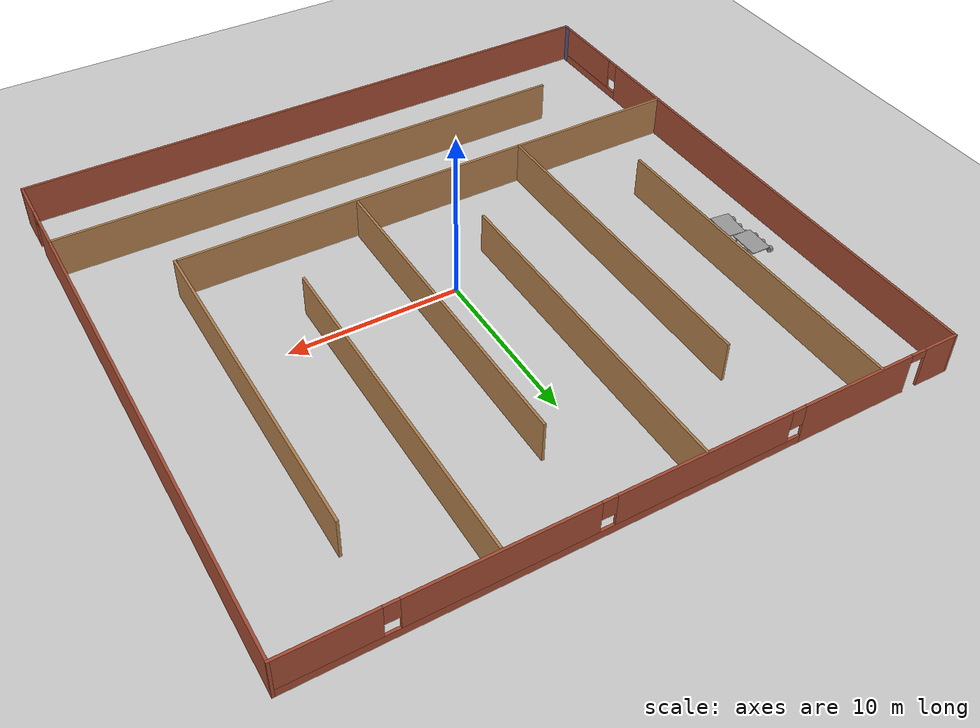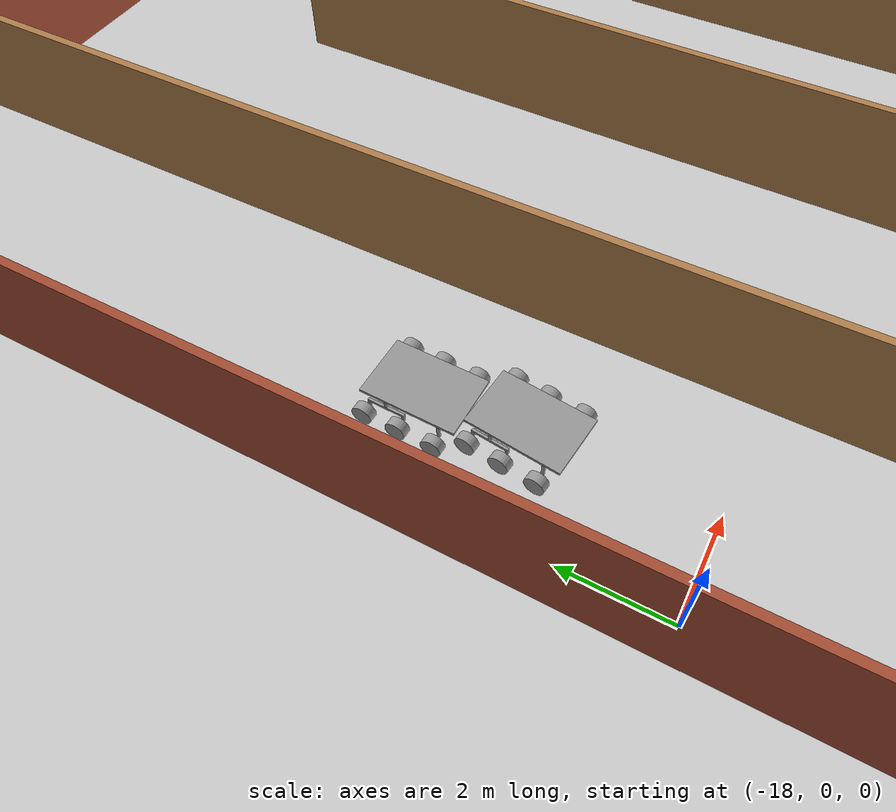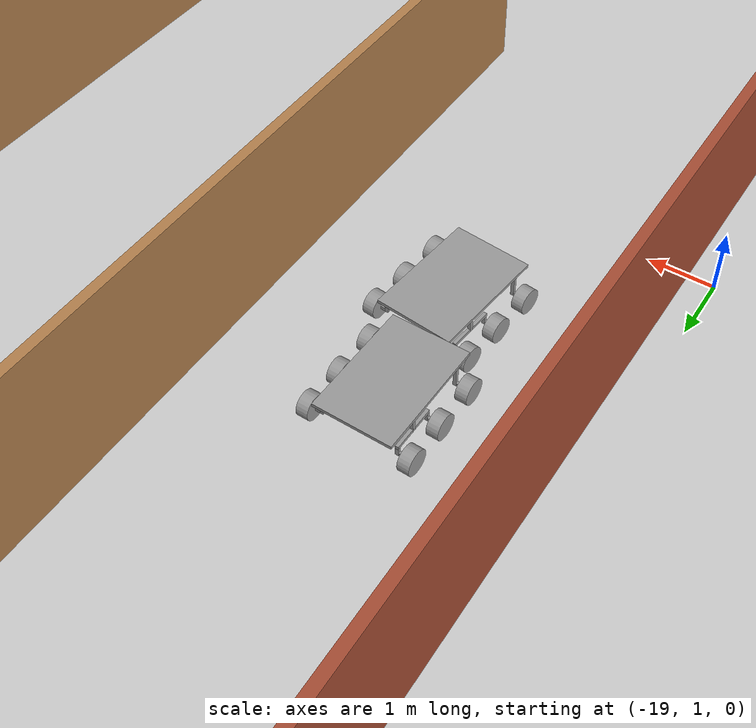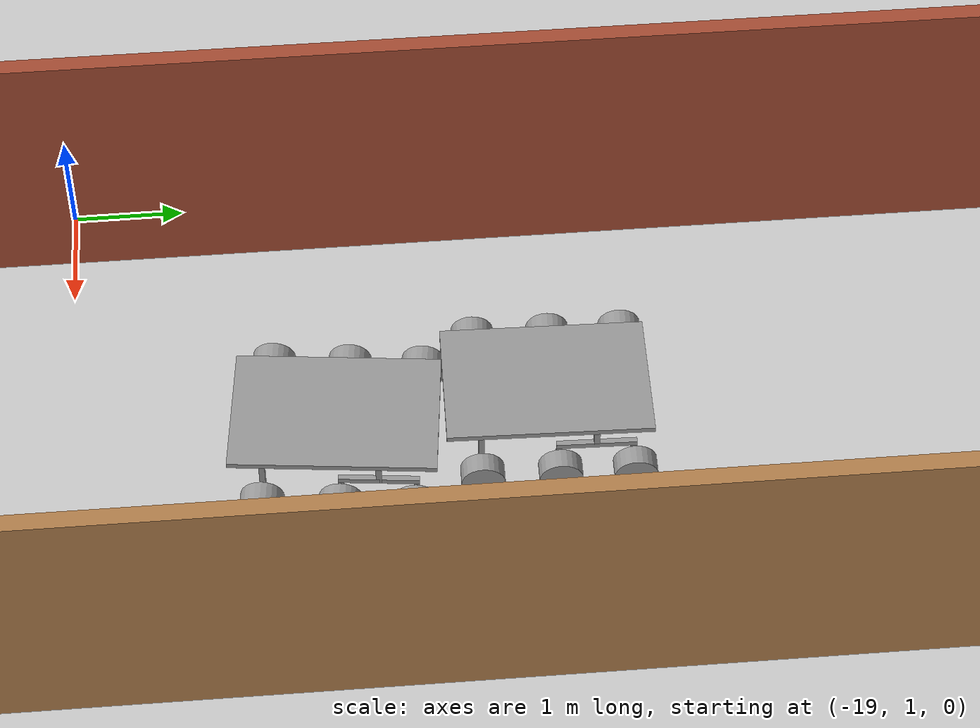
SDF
<sdf version="1.6">
 <world name="default">
  <light name="sun" type="directional">
   <pose>0 0 10 0 -0 0</pose>
   <diffuse>0.8 0.8 0.8 1</diffuse>
   <specular>0.2 0.2 0.2 1</specular>
   <attenuation>
    <range>1000</range>
    <constant>0.9</constant>
    <linear>0.01</linear>
    <quadratic>0.001</quadratic>
   </attenuation>
   <direction>-0.5 0.1 -0.9</direction>
  </light>
  <model name="ground_plane">
   <static>1</static>
   <link name="link">
    <collision name="collision">
     <geometry><plane><normal>0 0 1</normal><size>100 100</size></plane></geometry>
     <surface><friction><ode><mu>100</mu><mu2>50</mu2></ode></friction></surface>
    </collision>
    <visual name="visual">
     <cast_shadows>0</cast_shadows>
     <geometry><plane><normal>0 0 1</normal><size>100 100</size></plane></geometry>
     <material>
      <script><uri>file://media/materials/scripts/gazebo.material</uri><name>Gazebo/Grey</name></script>
     </material>
    </visual>
   </link>
  </model>
  <gravity>0 0 -9.8</gravity>
  <magnetic_field>6e-06 2.3e-05 -4.2e-05</magnetic_field>
  <atmosphere type="adiabatic"/>
  <physics name="default_physics" default="0" type="ode">
   <max_step_size>0.001</max_step_size>
   <real_time_factor>1</real_time_factor>
   <real_time_update_rate>1000</real_time_update_rate>
  </physics>
  <scene><ambient>0.4 0.4 0.4 1</ambient><background>0.7 0.7 0.7 1</background><shadows>1</shadows></scene>
  <spherical_coordinates>
   <surface_model>EARTH_WGS84</surface_model>
   <latitude_deg>0</latitude_deg>
   <longitude_deg>0</longitude_deg>
   <elevation>0</elevation>
   <heading_deg>0</heading_deg>
  </spherical_coordinates>
  <model name="Building1">
   <pose>0.018155 0.145217 0 0 -0 0</pose>
   <link name="Wall_135">
    <pose>0.005428 17.55 0 0 -0 0</pose>
    <visual name="Wall_135_Visual_0">
     <pose>-17.5623 0 1.25 0 -0 0</pose>
     <geometry><box><size>2.12549 0.15 2.5</size></box></geometry>
     <material>
      <script><uri>file://media/materials/scripts/gazebo.material</uri><name>Gazebo/Bricks</name></script>
      <ambient>0.333333 0.333333 0.498039 1</ambient>
     </material>
     <meta><layer>0</layer></meta>
    </visual>
    <collision name="Wall_135_Collision_0">
     <geometry><box><size>2.12549 0.15 2.5</size></box></geometry>
     <pose>-17.5623 0 1.25 0 -0 0</pose>
    </collision>
    <visual name="Wall_135_Visual_1">
     <pose>-12.2043 0 1.25 0 -0 0</pose>
     <geometry><box><size>6.79049 0.15 2.5</size></box></geometry>
     <material>
      <script><uri>file://media/materials/scripts/gazebo.material</uri><name>Gazebo/Bricks</name></script>
      <ambient>0.333333 0.333333 0.498039 1</ambient>
     </material>
     <meta><layer>0</layer></meta>
    </visual>
    <collision name="Wall_135_Collision_1">
     <geometry><box><size>6.79049 0.15 2.5</size></box></geometry>
     <pose>-12.2043 0 1.25 0 -0 0</pose>
    </collision>
    <visual name="Wall_135_Visual_2">
     <pose>4.90799 0 0.25 0 -0 0</pose>
     <geometry><box><size>27.434 0.15 0.5</size></box></geometry>
     <material>
      <script><uri>file://media/materials/scripts/gazebo.material</uri><name>Gazebo/Bricks</name></script>
      <ambient>0.333333 0.333333 0.498039 1</ambient>
     </material>
     <meta><layer>0</layer></meta>
    </visual>
    <collision name="Wall_135_Collision_2">
     <geometry><box><size>27.434 0.15 0.5</size></box></geometry>
     <pose>4.90799 0 0.25 0 -0 0</pose>
    </collision>
    <visual name="Wall_135_Visual_3">
     <pose>-3.02838 0 1.5 0 -0 0</pose>
     <geometry><box><size>9.96126 0.15 2</size></box></geometry>
     <material>
      <script><uri>file://media/materials/scripts/gazebo.material</uri><name>Gazebo/Bricks</name></script>
      <ambient>0.333333 0.333333 0.498039 1</ambient>
     </material>
     <meta><layer>0</layer></meta>
    </visual>
    <collision name="Wall_135_Collision_3">
     <geometry><box><size>9.96126 0.15 2</size></box></geometry>
     <pose>-3.02838 0 1.5 0 -0 0</pose>
    </collision>
    <visual name="Wall_135_Visual_4">
     <pose>7.73288 0 1.5 0 -0 0</pose>
     <geometry><box><size>9.96126 0.15 2</size></box></geometry>
     <material>
      <script><uri>file://media/materials/scripts/gazebo.material</uri><name>Gazebo/Bricks</name></script>
      <ambient>0.333333 0.333333 0.498039 1</ambient>
     </material>
     <meta><layer>0</layer></meta>
    </visual>
    <collision name="Wall_135_Collision_4">
     <geometry><box><size>9.96126 0.15 2</size></box></geometry>
     <pose>7.73288 0 1.5 0 -0 0</pose>
    </collision>
    <visual name="Wall_135_Visual_5">
     <pose>16.0693 0 1.5 0 -0 0</pose>
     <geometry><box><size>5.11148 0.15 2</size></box></geometry>
     <material>
      <script><uri>file://media/materials/scripts/gazebo.material</uri><name>Gazebo/Bricks</name></script>
      <ambient>0.333333 0.333333 0.498039 1</ambient>
     </material>
     <meta><layer>0</layer></meta>
    </visual>
    <collision name="Wall_135_Collision_5">
     <geometry><box><size>5.11148 0.15 2</size></box></geometry>
     <pose>16.0693 0 1.5 0 -0 0</pose>
    </collision>
    <visual name="Wall_135_Visual_6">
     <pose>-8.40901 0 1.9 0 -0 0</pose>
     <geometry><box><size>0.8 0.15 1.2</size></box></geometry>
     <material>
      <script><uri>file://media/materials/scripts/gazebo.material</uri><name>Gazebo/Bricks</name></script>
      <ambient>0.333333 0.333333 0.498039 1</ambient>
     </material>
     <meta><layer>0</layer></meta>
    </visual>
    <collision name="Wall_135_Collision_6">
     <geometry><box><size>0.8 0.15 1.2</size></box></geometry>
     <pose>-8.40901 0 1.9 0 -0 0</pose>
    </collision>
    <visual name="Wall_135_Visual_7">
     <pose>2.35225 0 1.9 0 -0 0</pose>
     <geometry><box><size>0.8 0.15 1.2</size></box></geometry>
     <material>
      <script><uri>file://media/materials/scripts/gazebo.material</uri><name>Gazebo/Bricks</name></script>
      <ambient>0.333333 0.333333 0.498039 1</ambient>
     </material>
     <meta><layer>0</layer></meta>
    </visual>
    <collision name="Wall_135_Collision_7">
     <geometry><box><size>0.8 0.15 1.2</size></box></geometry>
     <pose>2.35225 0 1.9 0 -0 0</pose>
    </collision>
    <visual name="Wall_135_Visual_8">
     <pose>13.1135 0 1.9 0 -0 0</pose>
     <geometry><box><size>0.8 0.15 1.2</size></box></geometry>
     <material>
      <script><uri>file://media/materials/scripts/gazebo.material</uri><name>Gazebo/Bricks</name></script>
      <ambient>0.333333 0.333333 0.498039 1</ambient>
     </material>
     <meta><layer>0</layer></meta>
    </visual>
    <collision name="Wall_135_Collision_8">
     <geometry><box><size>0.8 0.15 1.2</size></box></geometry>
     <pose>13.1135 0 1.9 0 -0 0</pose>
    </collision>
    <visual name="Wall_135_Visual_9">
     <pose>-16.0495 0 2.25 0 -0 0</pose>
     <geometry><box><size>0.9 0.15 0.5</size></box></geometry>
     <material>
      <script><uri>file://media/materials/scripts/gazebo.material</uri><name>Gazebo/Bricks</name></script>
      <ambient>0.333333 0.333333 0.498039 1</ambient>
     </material>
     <meta><layer>0</layer></meta>
    </visual>
    <collision name="Wall_135_Collision_9">
     <geometry><box><size>0.9 0.15 0.5</size></box></geometry>
     <pose>-16.0495 0 2.25 0 -0 0</pose>
    </collision>
   </link>
   <link name="Wall_138">
    <collision name="Wall_138_Collision">
     <geometry><box><size>20 0.15 2.5</size></box></geometry>
     <pose>0 0 1.25 0 -0 0</pose>
    </collision>
    <visual name="Wall_138_Visual">
     <pose>0 0 1.25 0 -0 0</pose>
     <geometry><box><size>20 0.15 2.5</size></box></geometry>
     <material>
      <script><uri>file://media/materials/scripts/gazebo.material</uri><name>Gazebo/Wood</name></script>
      <ambient>0.333333 0.333333 0.498039 1</ambient>
     </material>
     <meta><layer>0</layer></meta>
    </visual>
    <pose>-13.6766 7.55431 0 0 -0 -1.5708</pose>
   </link>
   <link name="Wall_140">
    <collision name="Wall_140_Collision">
     <geometry><box><size>19.75 0.15 2.5</size></box></geometry>
     <pose>0 0 1.25 0 -0 0</pose>
    </collision>
    <visual name="Wall_140_Visual">
     <pose>0 0 1.25 0 -0 0</pose>
     <geometry><box><size>19.75 0.15 2.5</size></box></geometry>
     <material>
      <script><uri>file://media/materials/scripts/gazebo.material</uri><name>Gazebo/Wood</name></script>
      <ambient>0.333333 0.333333 0.498039 1</ambient>
     </material>
     <meta><layer>0</layer></meta>
    </visual>
    <pose>-8.29597 2.63601 0 0 -0 1.5708</pose>
   </link>
   <link name="Wall_142">
    <collision name="Wall_142_Collision">
     <geometry><box><size>20 0.15 2.5</size></box></geometry>
     <pose>0 0 1.25 0 -0 0</pose>
    </collision>
    <visual name="Wall_142_Visual">
     <pose>0 0 1.25 0 -0 0</pose>
     <geometry><box><size>20 0.15 2.5</size></box></geometry>
     <material>
      <script><uri>file://media/materials/scripts/gazebo.material</uri><name>Gazebo/Wood</name></script>
      <ambient>0.333333 0.333333 0.498039 1</ambient>
     </material>
     <meta><layer>0</layer></meta>
    </visual>
    <pose>-3.02295 7.55431 0 0 -0 -1.5708</pose>
   </link>
   <link name="Wall_144">
    <collision name="Wall_144_Collision">
     <geometry><box><size>19.5 0.15 2.5</size></box></geometry>
     <pose>0 0 1.25 0 -0 0</pose>
    </collision>
    <visual name="Wall_144_Visual">
     <pose>0 0 1.25 0 -0 0</pose>
     <geometry><box><size>19.5 0.15 2.5</size></box></geometry>
     <material>
      <script><uri>file://media/materials/scripts/gazebo.material</uri><name>Gazebo/Wood</name></script>
      <ambient>0.333333 0.333333 0.498039 1</ambient>
     </material>
     <meta><layer>0</layer></meta>
    </visual>
    <pose>2.46529 2.72624 0 0 -0 1.5708</pose>
   </link>
   <link name="Wall_146">
    <collision name="Wall_146_Collision">
     <geometry><box><size>20 0.15 2.5</size></box></geometry>
     <pose>0 0 1.25 0 -0 0</pose>
    </collision>
    <visual name="Wall_146_Visual">
     <pose>0 0 1.25 0 -0 0</pose>
     <geometry><box><size>20 0.15 2.5</size></box></geometry>
     <material>
      <script><uri>file://media/materials/scripts/gazebo.material</uri><name>Gazebo/Wood</name></script>
      <ambient>0.333333 0.333333 0.498039 1</ambient>
     </material>
     <meta><layer>0</layer></meta>
    </visual>
    <pose>7.84593 7.44669 0 0 -0 -1.5708</pose>
   </link>
   <link name="Wall_149">
    <collision name="Wall_149_Collision">
     <geometry><box><size>20 0.15 2.5</size></box></geometry>
     <pose>0 0 1.25 0 -0 0</pose>
    </collision>
    <visual name="Wall_149_Visual">
     <pose>0 0 1.25 0 -0 0</pose>
     <geometry><box><size>20 0.15 2.5</size></box></geometry>
     <material>
      <script><uri>file://media/materials/scripts/gazebo.material</uri><name>Gazebo/Wood</name></script>
      <ambient>0.333333 0.333333 0.498039 1</ambient>
     </material>
     <meta><layer>0</layer></meta>
    </visual>
    <pose>13.2266 2.76101 0 0 -0 1.5708</pose>
   </link>
   <link name="Wall_152">
    <pose>18.5554 0 0 0 -0 -1.5708</pose>
    <visual name="Wall_152_Visual_0">
     <pose>-1.68906 0 1.25 0 -0 0</pose>
     <geometry><box><size>31.8719 0.15 2.5</size></box></geometry>
     <material>
      <script><uri>file://media/materials/scripts/gazebo.material</uri><name>Gazebo/Bricks</name></script>
      <ambient>0.333333 0.333333 0.498039 1</ambient>
     </material>
     <meta><layer>0</layer></meta>
    </visual>
    <collision name="Wall_152_Collision_0">
     <geometry><box><size>31.8719 0.15 2.5</size></box></geometry>
     <pose>-1.68906 0 1.25 0 -0 0</pose>
    </collision>
    <visual name="Wall_152_Visual_1">
     <pose>16.3859 0 1.25 0 -0 0</pose>
     <geometry><box><size>2.47813 0.15 2.5</size></box></geometry>
     <material>
      <script><uri>file://media/materials/scripts/gazebo.material</uri><name>Gazebo/Bricks</name></script>
      <ambient>0.333333 0.333333 0.498039 1</ambient>
     </material>
     <meta><layer>0</layer></meta>
    </visual>
    <collision name="Wall_152_Collision_1">
     <geometry><box><size>2.47813 0.15 2.5</size></box></geometry>
     <pose>16.3859 0 1.25 0 -0 0</pose>
    </collision>
    <visual name="Wall_152_Visual_2">
     <pose>14.6969 0 2.25 0 -0 0</pose>
     <geometry><box><size>0.9 0.15 0.5</size></box></geometry>
     <material>
      <script><uri>file://media/materials/scripts/gazebo.material</uri><name>Gazebo/Bricks</name></script>
      <ambient>0.333333 0.333333 0.498039 1</ambient>
     </material>
     <meta><layer>0</layer></meta>
    </visual>
    <collision name="Wall_152_Collision_2">
     <geometry><box><size>0.9 0.15 0.5</size></box></geometry>
     <pose>14.6969 0 2.25 0 -0 0</pose>
    </collision>
   </link>
   <link name="Wall_153">
    <collision name="Wall_153_Collision">
     <geometry><box><size>37.25 0.15 2.5</size></box></geometry>
     <pose>0 0 1.25 0 -0 0</pose>
    </collision>
    <visual name="Wall_153_Visual">
     <pose>0 0 1.25 0 -0 0</pose>
     <geometry><box><size>37.25 0.15 2.5</size></box></geometry>
     <material>
      <script><uri>file://media/materials/scripts/gazebo.material</uri><name>Gazebo/Bricks</name></script>
      <ambient>0.333333 0.333333 0.498039 1</ambient>
     </material>
     <meta><layer>0</layer></meta>
    </visual>
    <pose>0.005428 -17.55 0 0 -0 3.14159</pose>
   </link>
   <link name="Wall_154">
    <collision name="Wall_154_Collision">
     <geometry><box><size>0.55 0.15 2.5</size></box></geometry>
     <pose>0 0 1.25 0 -0 0</pose>
    </collision>
    <visual name="Wall_154_Visual">
     <pose>0 0 1.25 0 -0 0</pose>
     <geometry><box><size>0.55 0.15 2.5</size></box></geometry>
     <material>
      <script><uri>file://media/materials/scripts/gazebo.material</uri><name>Gazebo/Grey</name></script>
      <ambient>0.333333 0.333333 0.498039 1</ambient>
     </material>
     <meta><layer>0</layer></meta>
    </visual>
    <pose>-18.5446 -17.35 0 0 -0 1.5708</pose>
   </link>
   <link name="Wall_156">
    <collision name="Wall_156_Collision">
     <geometry><box><size>31.75 0.15 2.5</size></box></geometry>
     <pose>0 0 1.25 0 -0 0</pose>
    </collision>
    <visual name="Wall_156_Visual">
     <pose>0 0 1.25 0 -0 0</pose>
     <geometry><box><size>31.75 0.15 2.5</size></box></geometry>
     <material>
      <script><uri>file://media/materials/scripts/gazebo.material</uri><name>Gazebo/Wood</name></script>
      <ambient>0.333333 0.333333 0.498039 1</ambient>
     </material>
     <meta><layer>0</layer></meta>
    </visual>
    <pose>2.69958 -12.1142 0 0 -0 3.14159</pose>
   </link>
   <link name="Wall_47">
    <pose>-18.5446 0.2 0 0 -0 -1.5708</pose>
    <visual name="Wall_47_Visual_0">
     <pose>-2.80922 0 1.25 0 -0 0</pose>
     <geometry><box><size>29.2316 0.15 2.5</size></box></geometry>
     <material>
      <script><uri>file://media/materials/scripts/gazebo.material</uri><name>Gazebo/Bricks</name></script>
      <ambient>0.333333 0.333333 0.498039 1</ambient>
     </material>
     <meta><layer>0</layer></meta>
    </visual>
    <collision name="Wall_47_Collision_0">
     <geometry><box><size>29.2316 0.15 2.5</size></box></geometry>
     <pose>-2.80922 0 1.25 0 -0 0</pose>
    </collision>
    <visual name="Wall_47_Visual_1">
     <pose>14.6158 0 0.25 0 -0 0</pose>
     <geometry><box><size>5.61844 0.15 0.5</size></box></geometry>
     <material>
      <script><uri>file://media/materials/scripts/gazebo.material</uri><name>Gazebo/Bricks</name></script>
      <ambient>0.333333 0.333333 0.498039 1</ambient>
     </material>
     <meta><layer>0</layer></meta>
    </visual>
    <collision name="Wall_47_Collision_1">
     <geometry><box><size>5.61844 0.15 0.5</size></box></geometry>
     <pose>14.6158 0 0.25 0 -0 0</pose>
    </collision>
    <visual name="Wall_47_Visual_2">
     <pose>15.0158 0 1.5 0 -0 0</pose>
     <geometry><box><size>4.81844 0.15 2</size></box></geometry>
     <material>
      <script><uri>file://media/materials/scripts/gazebo.material</uri><name>Gazebo/Bricks</name></script>
      <ambient>0.333333 0.333333 0.498039 1</ambient>
     </material>
     <meta><layer>0</layer></meta>
    </visual>
    <collision name="Wall_47_Collision_2">
     <geometry><box><size>4.81844 0.15 2</size></box></geometry>
     <pose>15.0158 0 1.5 0 -0 0</pose>
    </collision>
    <visual name="Wall_47_Visual_3">
     <pose>12.2066 0 1.9 0 -0 0</pose>
     <geometry><box><size>0.8 0.15 1.2</size></box></geometry>
     <material>
      <script><uri>file://media/materials/scripts/gazebo.material</uri><name>Gazebo/Bricks</name></script>
      <ambient>0.333333 0.333333 0.498039 1</ambient>
     </material>
     <meta><layer>0</layer></meta>
    </visual>
    <collision name="Wall_47_Collision_3">
     <geometry><box><size>0.8 0.15 1.2</size></box></geometry>
     <pose>12.2066 0 1.9 0 -0 0</pose>
    </collision>
   </link>
   <link name="Wall_68">
    <collision name="Wall_68_Collision">
     <geometry><box><size>31.75 0.15 2.5</size></box></geometry>
     <pose>0 0 1.25 0 -0 0</pose>
    </collision>
    <visual name="Wall_68_Visual">
     <pose>0 0 1.25 0 -0 0</pose>
     <geometry><box><size>31.75 0.15 2.5</size></box></geometry>
     <material>
      <script><uri>file://media/materials/scripts/gazebo.material</uri><name>Gazebo/Wood</name></script>
      <ambient>0.333333 0.333333 0.498039 1</ambient>
     </material>
     <meta><layer>0</layer></meta>
    </visual>
    <pose>-2.75543 -7.17891 0 0 -0 3.14159</pose>
   </link>
   <static>1</static>
  </model>
  <model name="model1">
   <link name="link_0">
    <inertial>
     <mass>1</mass>
     <inertia>
      <ixx>0.166667</ixx>
      <ixy>0</ixy>
      <ixz>0</ixz>
      <iyy>0.166667</iyy>
      <iyz>0</iyz>
      <izz>0.166667</izz>
     </inertia>
    </inertial>
    <pose>0.453204 0.202085 0.600179 0 -0 0</pose>
    <visual name="visual">
     <geometry><box><size>1.2 1.8 0.05</size></box></geometry>
     <material>
      <lighting>1</lighting>
      <script><uri>file://media/materials/scripts/gazebo.material</uri><name>Gazebo/Grey</name></script>
      <shader type="pixel"><normal_map>__default__</normal_map></shader>
      <ambient>0.3 0.3 0.3 1</ambient>
      <diffuse>0.7 0.7 0.7 1</diffuse>
      <specular>0.01 0.01 0.01 1</specular>
      <emissive>0 0 0 1</emissive>
     </material>
    </visual>
    <collision name="collision">
     <geometry><box><size>1.2 1.8 0.05</size></box></geometry>
     <surface>
      <friction>
       <ode><mu>1</mu><mu2>1</mu2><fdir1>0 0 0</fdir1><slip1>0</slip1><slip2>0</slip2></ode>
       <torsional>
        <coefficient>1</coefficient>
        <patch_radius>0</patch_radius>
        <surface_radius>0</surface_radius>
        <use_patch_radius>1</use_patch_radius>
        <ode><slip>0</slip></ode>
       </torsional>
      </friction>
      <bounce><restitution_coefficient>0</restitution_coefficient><threshold>1e+06</threshold></bounce>
      <contact>
       <collide_without_contact>0</collide_without_contact>
       <collide_without_contact_bitmask>1</collide_without_contact_bitmask>
       <collide_bitmask>1</collide_bitmask>
       <ode>
        <soft_cfm>0</soft_cfm>
        <soft_erp>0.2</soft_erp>
        <kp>1e+13</kp>
        <kd>1</kd>
        <max_vel>0.01</max_vel>
        <min_depth>0</min_depth>
       </ode>
       <bullet>
        <split_impulse>1</split_impulse>
        <split_impulse_penetration_threshold>-0.01</split_impulse_penetration_threshold>
        <soft_cfm>0</soft_cfm>
        <soft_erp>0.2</soft_erp>
        <kp>1e+13</kp>
        <kd>1</kd>
       </bullet>
      </contact>
     </surface>
    </collision>
   </link>
   <link name="link_0_0_clone_clone_1">
    <inertial>
     <mass>1</mass>
     <inertia><ixx>0.145833</ixx><ixy>0</ixy><ixz>0</ixz><iyy>0.145833</iyy><iyz>0</iyz><izz>0.125</izz></inertia>
    </inertial>
    <pose>1.2232 -0.397915 0.300179 -3.14153 1.57079 -3.14153</pose>
    <visual name="visual_0">
     <geometry><cylinder><radius>0.19</radius><length>0.18</length></cylinder></geometry>
     <material>
      <lighting>1</lighting>
      <script><uri>file://media/materials/scripts/gazebo.material</uri><name>Gazebo/Grey</name></script>
      <shader type="pixel"><normal_map>__default__</normal_map></shader>
      <ambient>0.3 0.3 0.3 1</ambient>
      <diffuse>0.7 0.7 0.7 1</diffuse>
      <specular>0.01 0.01 0.01 1</specular>
      <emissive>0 0 0 1</emissive>
     </material>
    </visual>
    <collision name="collision">
     <geometry><cylinder><radius>0.19</radius><length>0.18</length></cylinder></geometry>
     <surface>
      <friction>
       <ode><mu>1</mu><mu2>1</mu2><fdir1>0 0 0</fdir1><slip1>0</slip1><slip2>0</slip2></ode>
       <torsional>
        <coefficient>1</coefficient>
        <patch_radius>0</patch_radius>
        <surface_radius>0</surface_radius>
        <use_patch_radius>1</use_patch_radius>
        <ode><slip>0</slip></ode>
       </torsional>
      </friction>
      <bounce><restitution_coefficient>0</restitution_coefficient><threshold>1e+06</threshold></bounce>
      <contact>
       <collide_without_contact>0</collide_without_contact>
       <collide_without_contact_bitmask>1</collide_without_contact_bitmask>
       <collide_bitmask>1</collide_bitmask>
       <ode>
        <soft_cfm>0</soft_cfm>
        <soft_erp>0.2</soft_erp>
        <kp>1e+13</kp>
        <kd>1</kd>
        <max_vel>0.01</max_vel>
        <min_depth>0</min_depth>
       </ode>
       <bullet>
        <split_impulse>1</split_impulse>
        <split_impulse_penetration_threshold>-0.01</split_impulse_penetration_threshold>
        <soft_cfm>0</soft_cfm>
        <soft_erp>0.2</soft_erp>
        <kp>1e+13</kp>
        <kd>1</kd>
       </bullet>
      </contact>
     </surface>
    </collision>
   </link>
   <link name="link_0_0_clone_clone_1_clone_0">
    <inertial>
     <mass>1</mass>
     <inertia><ixx>0.145833</ixx><ixy>0</ixy><ixz>0</ixz><iyy>0.145833</iyy><iyz>0</iyz><izz>0.125</izz></inertia>
    </inertial>
    <pose>1.2232 0.277085 0.30018 -3.14153 1.57079 -3.14153</pose>
    <visual name="visual_0">
     <geometry><cylinder><radius>0.19</radius><length>0.18</length></cylinder></geometry>
     <material>
      <lighting>1</lighting>
      <script><uri>file://media/materials/scripts/gazebo.material</uri><name>Gazebo/Grey</name></script>
      <shader type="pixel"><normal_map>__default__</normal_map></shader>
      <ambient>0.3 0.3 0.3 1</ambient>
      <diffuse>0.7 0.7 0.7 1</diffuse>
      <specular>0.01 0.01 0.01 1</specular>
      <emissive>0 0 0 1</emissive>
     </material>
    </visual>
    <collision name="collision">
     <geometry><cylinder><radius>0.19</radius><length>0.18</length></cylinder></geometry>
     <surface>
      <friction>
       <ode><mu>1</mu><mu2>1</mu2><fdir1>0 0 0</fdir1><slip1>0</slip1><slip2>0</slip2></ode>
       <torsional>
        <coefficient>1</coefficient>
        <patch_radius>0</patch_radius>
        <surface_radius>0</surface_radius>
        <use_patch_radius>1</use_patch_radius>
        <ode><slip>0</slip></ode>
       </torsional>
      </friction>
      <bounce><restitution_coefficient>0</restitution_coefficient><threshold>1e+06</threshold></bounce>
      <contact>
       <collide_without_contact>0</collide_without_contact>
       <collide_without_contact_bitmask>1</collide_without_contact_bitmask>
       <collide_bitmask>1</collide_bitmask>
       <ode>
        <soft_cfm>0</soft_cfm>
        <soft_erp>0.2</soft_erp>
        <kp>1e+13</kp>
        <kd>1</kd>
        <max_vel>0.01</max_vel>
        <min_depth>0</min_depth>
       </ode>
       <bullet>
        <split_impulse>1</split_impulse>
        <split_impulse_penetration_threshold>-0.01</split_impulse_penetration_threshold>
        <soft_cfm>0</soft_cfm>
        <soft_erp>0.2</soft_erp>
        <kp>1e+13</kp>
        <kd>1</kd>
       </bullet>
      </contact>
     </surface>
    </collision>
   </link>
   <link name="link_0_0_clone_clone_1_clone_1">
    <inertial>
     <mass>1</mass>
     <inertia><ixx>0.145833</ixx><ixy>0</ixy><ixz>0</ixz><iyy>0.145833</iyy><iyz>0</iyz><izz>0.125</izz></inertia>
    </inertial>
    <pose>1.2232 0.927085 0.30018 -3.14153 1.57079 -3.14153</pose>
    <visual name="visual_0">
     <geometry><cylinder><radius>0.19</radius><length>0.18</length></cylinder></geometry>
     <material>
      <lighting>1</lighting>
      <script><uri>file://media/materials/scripts/gazebo.material</uri><name>Gazebo/Grey</name></script>
      <shader type="pixel"><normal_map>__default__</normal_map></shader>
      <ambient>0.3 0.3 0.3 1</ambient>
      <diffuse>0.7 0.7 0.7 1</diffuse>
      <specular>0.01 0.01 0.01 1</specular>
      <emissive>0 0 0 1</emissive>
     </material>
    </visual>
    <collision name="collision">
     <geometry><cylinder><radius>0.19</radius><length>0.18</length></cylinder></geometry>
     <surface>
      <friction>
       <ode><mu>1</mu><mu2>1</mu2><fdir1>0 0 0</fdir1><slip1>0</slip1><slip2>0</slip2></ode>
       <torsional>
        <coefficient>1</coefficient>
        <patch_radius>0</patch_radius>
        <surface_radius>0</surface_radius>
        <use_patch_radius>1</use_patch_radius>
        <ode><slip>0</slip></ode>
       </torsional>
      </friction>
      <bounce><restitution_coefficient>0</restitution_coefficient><threshold>1e+06</threshold></bounce>
      <contact>
       <collide_without_contact>0</collide_without_contact>
       <collide_without_contact_bitmask>1</collide_without_contact_bitmask>
       <collide_bitmask>1</collide_bitmask>
       <ode>
        <soft_cfm>0</soft_cfm>
        <soft_erp>0.2</soft_erp>
        <kp>1e+13</kp>
        <kd>1</kd>
        <max_vel>0.01</max_vel>
        <min_depth>0</min_depth>
       </ode>
       <bullet>
        <split_impulse>1</split_impulse>
        <split_impulse_penetration_threshold>-0.01</split_impulse_penetration_threshold>
        <soft_cfm>0</soft_cfm>
        <soft_erp>0.2</soft_erp>
        <kp>1e+13</kp>
        <kd>1</kd>
       </bullet>
      </contact>
     </surface>
    </collision>
   </link>
   <link name="link_0_0_clone_clone_1_clone_clone_1">
    <inertial>
     <mass>1</mass>
     <inertia><ixx>0.145833</ixx><ixy>0</ixy><ixz>0</ixz><iyy>0.145833</iyy><iyz>0</iyz><izz>0.125</izz></inertia>
    </inertial>
    <pose>-0.319461 -0.397915 0.300179 3.14154 -1.57079 3.12758</pose>
    <visual name="visual_0">
     <geometry><cylinder><radius>0.19</radius><length>0.18</length></cylinder></geometry>
     <material>
      <lighting>1</lighting>
      <script><uri>file://media/materials/scripts/gazebo.material</uri><name>Gazebo/Grey</name></script>
      <shader type="pixel"><normal_map>__default__</normal_map></shader>
      <ambient>0.3 0.3 0.3 1</ambient>
      <diffuse>0.7 0.7 0.7 1</diffuse>
      <specular>0.01 0.01 0.01 1</specular>
      <emissive>0 0 0 1</emissive>
     </material>
    </visual>
    <collision name="collision">
     <geometry><cylinder><radius>0.19</radius><length>0.18</length></cylinder></geometry>
     <surface>
      <friction>
       <ode><mu>1</mu><mu2>1</mu2><fdir1>0 0 0</fdir1><slip1>0</slip1><slip2>0</slip2></ode>
       <torsional>
        <coefficient>1</coefficient>
        <patch_radius>0</patch_radius>
        <surface_radius>0</surface_radius>
        <use_patch_radius>1</use_patch_radius>
        <ode><slip>0</slip></ode>
       </torsional>
      </friction>
      <bounce><restitution_coefficient>0</restitution_coefficient><threshold>1e+06</threshold></bounce>
      <contact>
       <collide_without_contact>0</collide_without_contact>
       <collide_without_contact_bitmask>1</collide_without_contact_bitmask>
       <collide_bitmask>1</collide_bitmask>
       <ode>
        <soft_cfm>0</soft_cfm>
        <soft_erp>0.2</soft_erp>
        <kp>1e+13</kp>
        <kd>1</kd>
        <max_vel>0.01</max_vel>
        <min_depth>0</min_depth>
       </ode>
       <bullet>
        <split_impulse>1</split_impulse>
        <split_impulse_penetration_threshold>-0.01</split_impulse_penetration_threshold>
        <soft_cfm>0</soft_cfm>
        <soft_erp>0.2</soft_erp>
        <kp>1e+13</kp>
        <kd>1</kd>
       </bullet>
      </contact>
     </surface>
    </collision>
   </link>
   <link name="link_0_0_clone_clone_1_clone_clone_1_clone">
    <inertial>
     <mass>1</mass>
     <inertia><ixx>0.145833</ixx><ixy>0</ixy><ixz>0</ixz><iyy>0.145833</iyy><iyz>0</iyz><izz>0.125</izz></inertia>
    </inertial>
    <pose>-0.319461 0.277085 0.30018 3.14154 -1.57079 3.12758</pose>
    <visual name="visual_0">
     <geometry><cylinder><radius>0.19</radius><length>0.18</length></cylinder></geometry>
     <material>
      <lighting>1</lighting>
      <script><uri>file://media/materials/scripts/gazebo.material</uri><name>Gazebo/Grey</name></script>
      <shader type="pixel"><normal_map>__default__</normal_map></shader>
      <ambient>0.3 0.3 0.3 1</ambient>
      <diffuse>0.7 0.7 0.7 1</diffuse>
      <specular>0.01 0.01 0.01 1</specular>
      <emissive>0 0 0 1</emissive>
     </material>
    </visual>
    <collision name="collision">
     <geometry><cylinder><radius>0.19</radius><length>0.18</length></cylinder></geometry>
     <surface>
      <friction>
       <ode><mu>1</mu><mu2>1</mu2><fdir1>0 0 0</fdir1><slip1>0</slip1><slip2>0</slip2></ode>
       <torsional>
        <coefficient>1</coefficient>
        <patch_radius>0</patch_radius>
        <surface_radius>0</surface_radius>
        <use_patch_radius>1</use_patch_radius>
        <ode><slip>0</slip></ode>
       </torsional>
      </friction>
      <bounce><restitution_coefficient>0</restitution_coefficient><threshold>1e+06</threshold></bounce>
      <contact>
       <collide_without_contact>0</collide_without_contact>
       <collide_without_contact_bitmask>1</collide_without_contact_bitmask>
       <collide_bitmask>1</collide_bitmask>
       <ode>
        <soft_cfm>0</soft_cfm>
        <soft_erp>0.2</soft_erp>
        <kp>1e+13</kp>
        <kd>1</kd>
        <max_vel>0.01</max_vel>
        <min_depth>0</min_depth>
       </ode>
       <bullet>
        <split_impulse>1</split_impulse>
        <split_impulse_penetration_threshold>-0.01</split_impulse_penetration_threshold>
        <soft_cfm>0</soft_cfm>
        <soft_erp>0.2</soft_erp>
        <kp>1e+13</kp>
        <kd>1</kd>
       </bullet>
      </contact>
     </surface>
    </collision>
   </link>
   <link name="link_0_0_clone_clone_1_clone_clone_1_clone_0">
    <inertial>
     <mass>1</mass>
     <inertia><ixx>0.145833</ixx><ixy>0</ixy><ixz>0</ixz><iyy>0.145833</iyy><iyz>0</iyz><izz>0.125</izz></inertia>
    </inertial>
    <pose>-0.319461 0.927085 0.30018 3.14154 -1.57079 3.12758</pose>
    <visual name="visual_0">
     <geometry><cylinder><radius>0.19</radius><length>0.18</length></cylinder></geometry>
     <material>
      <lighting>1</lighting>
      <script><uri>file://media/materials/scripts/gazebo.material</uri><name>Gazebo/Grey</name></script>
      <shader type="pixel"><normal_map>__default__</normal_map></shader>
      <ambient>0.3 0.3 0.3 1</ambient>
      <diffuse>0.7 0.7 0.7 1</diffuse>
      <specular>0.01 0.01 0.01 1</specular>
      <emissive>0 0 0 1</emissive>
     </material>
    </visual>
    <collision name="collision">
     <geometry><cylinder><radius>0.19</radius><length>0.18</length></cylinder></geometry>
     <surface>
      <friction>
       <ode><mu>1</mu><mu2>1</mu2><fdir1>0 0 0</fdir1><slip1>0</slip1><slip2>0</slip2></ode>
       <torsional>
        <coefficient>1</coefficient>
        <patch_radius>0</patch_radius>
        <surface_radius>0</surface_radius>
        <use_patch_radius>1</use_patch_radius>
        <ode><slip>0</slip></ode>
       </torsional>
      </friction>
      <bounce><restitution_coefficient>0</restitution_coefficient><threshold>1e+06</threshold></bounce>
      <contact>
       <collide_without_contact>0</collide_without_contact>
       <collide_without_contact_bitmask>1</collide_without_contact_bitmask>
       <collide_bitmask>1</collide_bitmask>
       <ode>
        <soft_cfm>0</soft_cfm>
        <soft_erp>0.2</soft_erp>
        <kp>1e+13</kp>
        <kd>1</kd>
        <max_vel>0.01</max_vel>
        <min_depth>0</min_depth>
       </ode>
       <bullet>
        <split_impulse>1</split_impulse>
        <split_impulse_penetration_threshold>-0.01</split_impulse_penetration_threshold>
        <soft_cfm>0</soft_cfm>
        <soft_erp>0.2</soft_erp>
        <kp>1e+13</kp>
        <kd>1</kd>
       </bullet>
      </contact>
     </surface>
    </collision>
   </link>
   <link name="link_1_clone">
    <inertial>
     <mass>1</mass>
     <inertia>
      <ixx>0.166667</ixx>
      <ixy>0</ixy>
      <ixz>0</ixz>
      <iyy>0.166667</iyy>
      <iyz>0</iyz>
      <izz>0.166667</izz>
     </inertia>
    </inertial>
    <pose>-0.121796 0.602085 0.485179 0 -0 0</pose>
    <visual name="visual">
     <geometry><box><size>0.05 0.05 0.18</size></box></geometry>
     <material>
      <lighting>1</lighting>
      <script><uri>file://media/materials/scripts/gazebo.material</uri><name>Gazebo/Grey</name></script>
      <shader type="pixel"><normal_map>__default__</normal_map></shader>
      <ambient>0.3 0.3 0.3 1</ambient>
      <diffuse>0.7 0.7 0.7 1</diffuse>
      <specular>0.01 0.01 0.01 1</specular>
      <emissive>0 0 0 1</emissive>
     </material>
    </visual>
    <collision name="collision">
     <geometry><box><size>0.05 0.05 0.18</size></box></geometry>
     <surface>
      <friction>
       <ode><mu>1</mu><mu2>1</mu2><fdir1>0 0 0</fdir1><slip1>0</slip1><slip2>0</slip2></ode>
       <torsional>
        <coefficient>1</coefficient>
        <patch_radius>0</patch_radius>
        <surface_radius>0</surface_radius>
        <use_patch_radius>1</use_patch_radius>
        <ode><slip>0</slip></ode>
       </torsional>
      </friction>
      <bounce><restitution_coefficient>0</restitution_coefficient><threshold>1e+06</threshold></bounce>
      <contact>
       <collide_without_contact>0</collide_without_contact>
       <collide_without_contact_bitmask>1</collide_without_contact_bitmask>
       <collide_bitmask>1</collide_bitmask>
       <ode>
        <soft_cfm>0</soft_cfm>
        <soft_erp>0.2</soft_erp>
        <kp>1e+13</kp>
        <kd>1</kd>
        <max_vel>0.01</max_vel>
        <min_depth>0</min_depth>
       </ode>
       <bullet>
        <split_impulse>1</split_impulse>
        <split_impulse_penetration_threshold>-0.01</split_impulse_penetration_threshold>
        <soft_cfm>0</soft_cfm>
        <soft_erp>0.2</soft_erp>
        <kp>1e+13</kp>
        <kd>1</kd>
       </bullet>
      </contact>
     </surface>
    </collision>
   </link>
   <link name="link_1_clone_0">
    <inertial>
     <mass>1</mass>
     <inertia>
      <ixx>0.166667</ixx>
      <ixy>0</ixy>
      <ixz>0</ixz>
      <iyy>0.166667</iyy>
      <iyz>0</iyz>
      <izz>0.166667</izz>
     </inertia>
    </inertial>
    <pose>1.0282 -0.397915 0.425179 0 -0 0</pose>
    <visual name="visual">
     <geometry><box><size>0.05 0.05 0.3</size></box></geometry>
     <material>
      <lighting>1</lighting>
      <script><uri>file://media/materials/scripts/gazebo.material</uri><name>Gazebo/Grey</name></script>
      <shader type="pixel"><normal_map>__default__</normal_map></shader>
      <ambient>0.3 0.3 0.3 1</ambient>
      <diffuse>0.7 0.7 0.7 1</diffuse>
      <specular>0.01 0.01 0.01 1</specular>
      <emissive>0 0 0 1</emissive>
     </material>
    </visual>
    <collision name="collision">
     <geometry><box><size>0.05 0.05 0.3</size></box></geometry>
     <surface>
      <friction>
       <ode><mu>1</mu><mu2>1</mu2><fdir1>0 0 0</fdir1><slip1>0</slip1><slip2>0</slip2></ode>
       <torsional>
        <coefficient>1</coefficient>
        <patch_radius>0</patch_radius>
        <surface_radius>0</surface_radius>
        <use_patch_radius>1</use_patch_radius>
        <ode><slip>0</slip></ode>
       </torsional>
      </friction>
      <bounce><restitution_coefficient>0</restitution_coefficient><threshold>1e+06</threshold></bounce>
      <contact>
       <collide_without_contact>0</collide_without_contact>
       <collide_without_contact_bitmask>1</collide_without_contact_bitmask>
       <collide_bitmask>1</collide_bitmask>
       <ode>
        <soft_cfm>0</soft_cfm>
        <soft_erp>0.2</soft_erp>
        <kp>1e+13</kp>
        <kd>1</kd>
        <max_vel>0.01</max_vel>
        <min_depth>0</min_depth>
       </ode>
       <bullet>
        <split_impulse>1</split_impulse>
        <split_impulse_penetration_threshold>-0.01</split_impulse_penetration_threshold>
        <soft_cfm>0</soft_cfm>
        <soft_erp>0.2</soft_erp>
        <kp>1e+13</kp>
        <kd>1</kd>
       </bullet>
      </contact>
     </surface>
    </collision>
   </link>
   <link name="link_1_clone_0_clone">
    <inertial>
     <mass>1</mass>
     <inertia>
      <ixx>0.166667</ixx>
      <ixy>0</ixy>
      <ixz>0</ixz>
      <iyy>0.166667</iyy>
      <iyz>0</iyz>
      <izz>0.166667</izz>
     </inertia>
    </inertial>
    <pose>1.0282 0.602085 0.485179 3.14159 -0 0</pose>
    <visual name="visual">
     <geometry><box><size>0.05 0.05 0.18</size></box></geometry>
     <material>
      <lighting>1</lighting>
      <script><uri>file://media/materials/scripts/gazebo.material</uri><name>Gazebo/Grey</name></script>
      <shader type="pixel"><normal_map>__default__</normal_map></shader>
      <ambient>0.3 0.3 0.3 1</ambient>
      <diffuse>0.7 0.7 0.7 1</diffuse>
      <specular>0.01 0.01 0.01 1</specular>
      <emissive>0 0 0 1</emissive>
     </material>
    </visual>
    <collision name="collision">
     <geometry><box><size>0.05 0.05 0.18</size></box></geometry>
     <surface>
      <friction>
       <ode><mu>1</mu><mu2>1</mu2><fdir1>0 0 0</fdir1><slip1>0</slip1><slip2>0</slip2></ode>
       <torsional>
        <coefficient>1</coefficient>
        <patch_radius>0</patch_radius>
        <surface_radius>0</surface_radius>
        <use_patch_radius>1</use_patch_radius>
        <ode><slip>0</slip></ode>
       </torsional>
      </friction>
      <bounce><restitution_coefficient>0</restitution_coefficient><threshold>1e+06</threshold></bounce>
      <contact>
       <collide_without_contact>0</collide_without_contact>
       <collide_without_contact_bitmask>1</collide_without_contact_bitmask>
       <collide_bitmask>1</collide_bitmask>
       <ode>
        <soft_cfm>0</soft_cfm>
        <soft_erp>0.2</soft_erp>
        <kp>1e+13</kp>
        <kd>1</kd>
        <max_vel>0.01</max_vel>
        <min_depth>0</min_depth>
       </ode>
       <bullet>
        <split_impulse>1</split_impulse>
        <split_impulse_penetration_threshold>-0.01</split_impulse_penetration_threshold>
        <soft_cfm>0</soft_cfm>
        <soft_erp>0.2</soft_erp>
        <kp>1e+13</kp>
        <kd>1</kd>
       </bullet>
      </contact>
     </surface>
    </collision>
   </link>
   <link name="link_1_clone_1">
    <inertial>
     <mass>1</mass>
     <inertia>
      <ixx>0.166667</ixx>
      <ixy>0</ixy>
      <ixz>0</ixz>
      <iyy>0.166667</iyy>
      <iyz>0</iyz>
      <izz>0.166667</izz>
     </inertia>
    </inertial>
    <pose>-0.121796 -0.397915 0.425179 0 -0 0</pose>
    <visual name="visual">
     <geometry><box><size>0.05 0.05 0.3</size></box></geometry>
     <material>
      <lighting>1</lighting>
      <script><uri>file://media/materials/scripts/gazebo.material</uri><name>Gazebo/Grey</name></script>
      <shader type="pixel"><normal_map>__default__</normal_map></shader>
      <ambient>0.3 0.3 0.3 1</ambient>
      <diffuse>0.7 0.7 0.7 1</diffuse>
      <specular>0.01 0.01 0.01 1</specular>
      <emissive>0 0 0 1</emissive>
     </material>
    </visual>
    <collision name="collision">
     <geometry><box><size>0.05 0.05 0.3</size></box></geometry>
     <surface>
      <friction>
       <ode><mu>1</mu><mu2>1</mu2><fdir1>0 0 0</fdir1><slip1>0</slip1><slip2>0</slip2></ode>
       <torsional>
        <coefficient>1</coefficient>
        <patch_radius>0</patch_radius>
        <surface_radius>0</surface_radius>
        <use_patch_radius>1</use_patch_radius>
        <ode><slip>0</slip></ode>
       </torsional>
      </friction>
      <bounce><restitution_coefficient>0</restitution_coefficient><threshold>1e+06</threshold></bounce>
      <contact>
       <collide_without_contact>0</collide_without_contact>
       <collide_without_contact_bitmask>1</collide_without_contact_bitmask>
       <collide_bitmask>1</collide_bitmask>
       <ode>
        <soft_cfm>0</soft_cfm>
        <soft_erp>0.2</soft_erp>
        <kp>1e+13</kp>
        <kd>1</kd>
        <max_vel>0.01</max_vel>
        <min_depth>0</min_depth>
       </ode>
       <bullet>
        <split_impulse>1</split_impulse>
        <split_impulse_penetration_threshold>-0.01</split_impulse_penetration_threshold>
        <soft_cfm>0</soft_cfm>
        <soft_erp>0.2</soft_erp>
        <kp>1e+13</kp>
        <kd>1</kd>
       </bullet>
      </contact>
     </surface>
    </collision>
   </link>
   <link name="link_1_clone_2">
    <inertial>
     <mass>1</mass>
     <inertia>
      <ixx>0.166667</ixx>
      <ixy>0</ixy>
      <ixz>0</ixz>
      <iyy>0.166667</iyy>
      <iyz>0</iyz>
      <izz>0.166667</izz>
     </inertia>
    </inertial>
    <pose>1.0282 0.927085 0.33518 0 -0 0</pose>
    <visual name="visual">
     <geometry><box><size>0.05 0.05 0.12</size></box></geometry>
     <material>
      <lighting>1</lighting>
      <script><uri>file://media/materials/scripts/gazebo.material</uri><name>Gazebo/Grey</name></script>
      <shader type="pixel"><normal_map>__default__</normal_map></shader>
      <ambient>0.3 0.3 0.3 1</ambient>
      <diffuse>0.7 0.7 0.7 1</diffuse>
      <specular>0.01 0.01 0.01 1</specular>
      <emissive>0 0 0 1</emissive>
     </material>
    </visual>
    <collision name="collision">
     <geometry><box><size>0.05 0.05 0.12</size></box></geometry>
     <surface>
      <friction>
       <ode><mu>1</mu><mu2>1</mu2><fdir1>0 0 0</fdir1><slip1>0</slip1><slip2>0</slip2></ode>
       <torsional>
        <coefficient>1</coefficient>
        <patch_radius>0</patch_radius>
        <surface_radius>0</surface_radius>
        <use_patch_radius>1</use_patch_radius>
        <ode><slip>0</slip></ode>
       </torsional>
      </friction>
      <bounce><restitution_coefficient>0</restitution_coefficient><threshold>1e+06</threshold></bounce>
      <contact>
       <collide_without_contact>0</collide_without_contact>
       <collide_without_contact_bitmask>1</collide_without_contact_bitmask>
       <collide_bitmask>1</collide_bitmask>
       <ode>
        <soft_cfm>0</soft_cfm>
        <soft_erp>0.2</soft_erp>
        <kp>1e+13</kp>
        <kd>1</kd>
        <max_vel>0.01</max_vel>
        <min_depth>0</min_depth>
       </ode>
       <bullet>
        <split_impulse>1</split_impulse>
        <split_impulse_penetration_threshold>-0.01</split_impulse_penetration_threshold>
        <soft_cfm>0</soft_cfm>
        <soft_erp>0.2</soft_erp>
        <kp>1e+13</kp>
        <kd>1</kd>
       </bullet>
      </contact>
     </surface>
    </collision>
   </link>
   <link name="link_1_clone_3">
    <inertial>
     <mass>1</mass>
     <inertia>
      <ixx>0.166667</ixx>
      <ixy>0</ixy>
      <ixz>0</ixz>
      <iyy>0.166667</iyy>
      <iyz>0</iyz>
      <izz>0.166667</izz>
     </inertia>
    </inertial>
    <pose>1.0282 0.277085 0.33518 0 -0 0</pose>
    <visual name="visual">
     <geometry><box><size>0.05 0.05 0.12</size></box></geometry>
     <material>
      <lighting>1</lighting>
      <script><uri>file://media/materials/scripts/gazebo.material</uri><name>Gazebo/Grey</name></script>
      <shader type="pixel"><normal_map>__default__</normal_map></shader>
      <ambient>0.3 0.3 0.3 1</ambient>
      <diffuse>0.7 0.7 0.7 1</diffuse>
      <specular>0.01 0.01 0.01 1</specular>
      <emissive>0 0 0 1</emissive>
     </material>
    </visual>
    <collision name="collision">
     <geometry><box><size>0.05 0.05 0.12</size></box></geometry>
     <surface>
      <friction>
       <ode><mu>1</mu><mu2>1</mu2><fdir1>0 0 0</fdir1><slip1>0</slip1><slip2>0</slip2></ode>
       <torsional>
        <coefficient>1</coefficient>
        <patch_radius>0</patch_radius>
        <surface_radius>0</surface_radius>
        <use_patch_radius>1</use_patch_radius>
        <ode><slip>0</slip></ode>
       </torsional>
      </friction>
      <bounce><restitution_coefficient>0</restitution_coefficient><threshold>1e+06</threshold></bounce>
      <contact>
       <collide_without_contact>0</collide_without_contact>
       <collide_without_contact_bitmask>1</collide_without_contact_bitmask>
       <collide_bitmask>1</collide_bitmask>
       <ode>
        <soft_cfm>0</soft_cfm>
        <soft_erp>0.2</soft_erp>
        <kp>1e+13</kp>
        <kd>1</kd>
        <max_vel>0.01</max_vel>
        <min_depth>0</min_depth>
       </ode>
       <bullet>
        <split_impulse>1</split_impulse>
        <split_impulse_penetration_threshold>-0.01</split_impulse_penetration_threshold>
        <soft_cfm>0</soft_cfm>
        <soft_erp>0.2</soft_erp>
        <kp>1e+13</kp>
        <kd>1</kd>
       </bullet>
      </contact>
     </surface>
    </collision>
   </link>
   <link name="link_1_clone_3_clone">
    <inertial>
     <mass>1</mass>
     <inertia>
      <ixx>0.166667</ixx>
      <ixy>0</ixy>
      <ixz>0</ixz>
      <iyy>0.166667</iyy>
      <iyz>0</iyz>
      <izz>0.166667</izz>
     </inertia>
    </inertial>
    <pose>-0.121796 0.927085 0.33518 0 -0 0</pose>
    <visual name="visual">
     <geometry><box><size>0.05 0.05 0.12</size></box></geometry>
     <material>
      <lighting>1</lighting>
      <script><uri>file://media/materials/scripts/gazebo.material</uri><name>Gazebo/Grey</name></script>
      <shader type="pixel"><normal_map>__default__</normal_map></shader>
      <ambient>0.3 0.3 0.3 1</ambient>
      <diffuse>0.7 0.7 0.7 1</diffuse>
      <specular>0.01 0.01 0.01 1</specular>
      <emissive>0 0 0 1</emissive>
     </material>
    </visual>
    <collision name="collision">
     <geometry><box><size>0.05 0.05 0.12</size></box></geometry>
     <surface>
      <friction>
       <ode><mu>1</mu><mu2>1</mu2><fdir1>0 0 0</fdir1><slip1>0</slip1><slip2>0</slip2></ode>
       <torsional>
        <coefficient>1</coefficient>
        <patch_radius>0</patch_radius>
        <surface_radius>0</surface_radius>
        <use_patch_radius>1</use_patch_radius>
        <ode><slip>0</slip></ode>
       </torsional>
      </friction>
      <bounce><restitution_coefficient>0</restitution_coefficient><threshold>1e+06</threshold></bounce>
      <contact>
       <collide_without_contact>0</collide_without_contact>
       <collide_without_contact_bitmask>1</collide_without_contact_bitmask>
       <collide_bitmask>1</collide_bitmask>
       <ode>
        <soft_cfm>0</soft_cfm>
        <soft_erp>0.2</soft_erp>
        <kp>1e+13</kp>
        <kd>1</kd>
        <max_vel>0.01</max_vel>
        <min_depth>0</min_depth>
       </ode>
       <bullet>
        <split_impulse>1</split_impulse>
        <split_impulse_penetration_threshold>-0.01</split_impulse_penetration_threshold>
        <soft_cfm>0</soft_cfm>
        <soft_erp>0.2</soft_erp>
        <kp>1e+13</kp>
        <kd>1</kd>
       </bullet>
      </contact>
     </surface>
    </collision>
   </link>
   <link name="link_1_clone_3_clone_0">
    <inertial>
     <mass>1</mass>
     <inertia>
      <ixx>0.166667</ixx>
      <ixy>0</ixy>
      <ixz>0</ixz>
      <iyy>0.166667</iyy>
      <iyz>0</iyz>
      <izz>0.166667</izz>
     </inertia>
    </inertial>
    <pose>-0.121796 0.277085 0.33518 0 -0 0</pose>
    <visual name="visual">
     <geometry><box><size>0.05 0.05 0.12</size></box></geometry>
     <material>
      <lighting>1</lighting>
      <script><uri>file://media/materials/scripts/gazebo.material</uri><name>Gazebo/Grey</name></script>
      <shader type="pixel"><normal_map>__default__</normal_map></shader>
      <ambient>0.3 0.3 0.3 1</ambient>
      <diffuse>0.7 0.7 0.7 1</diffuse>
      <specular>0.01 0.01 0.01 1</specular>
      <emissive>0 0 0 1</emissive>
     </material>
    </visual>
    <collision name="collision">
     <geometry><box><size>0.05 0.05 0.12</size></box></geometry>
     <surface>
      <friction>
       <ode><mu>1</mu><mu2>1</mu2><fdir1>0 0 0</fdir1><slip1>0</slip1><slip2>0</slip2></ode>
       <torsional>
        <coefficient>1</coefficient>
        <patch_radius>0</patch_radius>
        <surface_radius>0</surface_radius>
        <use_patch_radius>1</use_patch_radius>
        <ode><slip>0</slip></ode>
       </torsional>
      </friction>
      <bounce><restitution_coefficient>0</restitution_coefficient><threshold>1e+06</threshold></bounce>
      <contact>
       <collide_without_contact>0</collide_without_contact>
       <collide_without_contact_bitmask>1</collide_without_contact_bitmask>
       <collide_bitmask>1</collide_bitmask>
       <ode>
        <soft_cfm>0</soft_cfm>
        <soft_erp>0.2</soft_erp>
        <kp>1e+13</kp>
        <kd>1</kd>
        <max_vel>0.01</max_vel>
        <min_depth>0</min_depth>
       </ode>
       <bullet>
        <split_impulse>1</split_impulse>
        <split_impulse_penetration_threshold>-0.01</split_impulse_penetration_threshold>
        <soft_cfm>0</soft_cfm>
        <soft_erp>0.2</soft_erp>
        <kp>1e+13</kp>
        <kd>1</kd>
       </bullet>
      </contact>
     </surface>
    </collision>
   </link>
   <link name="link_2">
    <inertial>
     <mass>1</mass>
     <inertia>
      <ixx>0.166667</ixx>
      <ixy>0</ixy>
      <ixz>0</ixz>
      <iyy>0.166667</iyy>
      <iyz>0</iyz>
      <izz>0.166667</izz>
     </inertia>
    </inertial>
    <pose>1.0282 0.602085 0.42018 0 -0 0</pose>
    <visual name="visual">
     <geometry><box><size>0.05 0.7 0.05</size></box></geometry>
     <material>
      <lighting>1</lighting>
      <script><uri>file://media/materials/scripts/gazebo.material</uri><name>Gazebo/Grey</name></script>
      <shader type="pixel"><normal_map>__default__</normal_map></shader>
      <ambient>0.3 0.3 0.3 1</ambient>
      <diffuse>0.7 0.7 0.7 1</diffuse>
      <specular>0.01 0.01 0.01 1</specular>
      <emissive>0 0 0 1</emissive>
     </material>
    </visual>
    <collision name="collision">
     <geometry><box><size>0.05 0.7 0.05</size></box></geometry>
     <surface>
      <friction>
       <ode><mu>1</mu><mu2>1</mu2><fdir1>0 0 0</fdir1><slip1>0</slip1><slip2>0</slip2></ode>
       <torsional>
        <coefficient>1</coefficient>
        <patch_radius>0</patch_radius>
        <surface_radius>0</surface_radius>
        <use_patch_radius>1</use_patch_radius>
        <ode><slip>0</slip></ode>
       </torsional>
      </friction>
      <bounce><restitution_coefficient>0</restitution_coefficient><threshold>1e+06</threshold></bounce>
      <contact>
       <collide_without_contact>0</collide_without_contact>
       <collide_without_contact_bitmask>1</collide_without_contact_bitmask>
       <collide_bitmask>1</collide_bitmask>
       <ode>
        <soft_cfm>0</soft_cfm>
        <soft_erp>0.2</soft_erp>
        <kp>1e+13</kp>
        <kd>1</kd>
        <max_vel>0.01</max_vel>
        <min_depth>0</min_depth>
       </ode>
       <bullet>
        <split_impulse>1</split_impulse>
        <split_impulse_penetration_threshold>-0.01</split_impulse_penetration_threshold>
        <soft_cfm>0</soft_cfm>
        <soft_erp>0.2</soft_erp>
        <kp>1e+13</kp>
        <kd>1</kd>
       </bullet>
      </contact>
     </surface>
    </collision>
   </link>
   <link name="link_2_clone">
    <inertial>
     <mass>1</mass>
     <inertia>
      <ixx>0.166667</ixx>
      <ixy>0</ixy>
      <ixz>0</ixz>
      <iyy>0.166667</iyy>
      <iyz>0</iyz>
      <izz>0.166667</izz>
     </inertia>
    </inertial>
    <pose>-0.121796 0.602085 0.42018 0 -0 0</pose>
    <visual name="visual">
     <geometry><box><size>0.05 0.7 0.05</size></box></geometry>
     <material>
      <lighting>1</lighting>
      <script><uri>file://media/materials/scripts/gazebo.material</uri><name>Gazebo/Grey</name></script>
      <shader type="pixel"><normal_map>__default__</normal_map></shader>
      <ambient>0.3 0.3 0.3 1</ambient>
      <diffuse>0.7 0.7 0.7 1</diffuse>
      <specular>0.01 0.01 0.01 1</specular>
      <emissive>0 0 0 1</emissive>
     </material>
    </visual>
    <collision name="collision">
     <geometry><box><size>0.05 0.7 0.05</size></box></geometry>
     <surface>
      <friction>
       <ode><mu>1</mu><mu2>1</mu2><fdir1>0 0 0</fdir1><slip1>0</slip1><slip2>0</slip2></ode>
       <torsional>
        <coefficient>1</coefficient>
        <patch_radius>0</patch_radius>
        <surface_radius>0</surface_radius>
        <use_patch_radius>1</use_patch_radius>
        <ode><slip>0</slip></ode>
       </torsional>
      </friction>
      <bounce><restitution_coefficient>0</restitution_coefficient><threshold>1e+06</threshold></bounce>
      <contact>
       <collide_without_contact>0</collide_without_contact>
       <collide_without_contact_bitmask>1</collide_without_contact_bitmask>
       <collide_bitmask>1</collide_bitmask>
       <ode>
        <soft_cfm>0</soft_cfm>
        <soft_erp>0.2</soft_erp>
        <kp>1e+13</kp>
        <kd>1</kd>
        <max_vel>0.01</max_vel>
        <min_depth>0</min_depth>
       </ode>
       <bullet>
        <split_impulse>1</split_impulse>
        <split_impulse_penetration_threshold>-0.01</split_impulse_penetration_threshold>
        <soft_cfm>0</soft_cfm>
        <soft_erp>0.2</soft_erp>
        <kp>1e+13</kp>
        <kd>1</kd>
       </bullet>
      </contact>
     </surface>
    </collision>
   </link>
   <link name="link_4_clone_0_clone">
    <inertial>
     <mass>1</mass>
     <inertia>
      <ixx>0.166667</ixx>
      <ixy>0</ixy>
      <ixz>0</ixz>
      <iyy>0.166667</iyy>
      <iyz>0</iyz>
      <izz>0.166667</izz>
     </inertia>
    </inertial>
    <pose>1.0932 0.927085 0.30018 0 -0 0</pose>
    <visual name="visual">
     <geometry><box><size>0.08 0.05 0.05</size></box></geometry>
     <material>
      <lighting>1</lighting>
      <script><uri>file://media/materials/scripts/gazebo.material</uri><name>Gazebo/Grey</name></script>
      <shader type="pixel"><normal_map>__default__</normal_map></shader>
      <ambient>0.3 0.3 0.3 1</ambient>
      <diffuse>0.7 0.7 0.7 1</diffuse>
      <specular>0.01 0.01 0.01 1</specular>
      <emissive>0 0 0 1</emissive>
     </material>
    </visual>
    <collision name="collision">
     <geometry><box><size>0.08 0.05 0.05</size></box></geometry>
     <surface>
      <friction>
       <ode><mu>1</mu><mu2>1</mu2><fdir1>0 0 0</fdir1><slip1>0</slip1><slip2>0</slip2></ode>
       <torsional>
        <coefficient>1</coefficient>
        <patch_radius>0</patch_radius>
        <surface_radius>0</surface_radius>
        <use_patch_radius>1</use_patch_radius>
        <ode><slip>0</slip></ode>
       </torsional>
      </friction>
      <bounce><restitution_coefficient>0</restitution_coefficient><threshold>1e+06</threshold></bounce>
      <contact>
       <collide_without_contact>0</collide_without_contact>
       <collide_without_contact_bitmask>1</collide_without_contact_bitmask>
       <collide_bitmask>1</collide_bitmask>
       <ode>
        <soft_cfm>0</soft_cfm>
        <soft_erp>0.2</soft_erp>
        <kp>1e+13</kp>
        <kd>1</kd>
        <max_vel>0.01</max_vel>
        <min_depth>0</min_depth>
       </ode>
       <bullet>
        <split_impulse>1</split_impulse>
        <split_impulse_penetration_threshold>-0.01</split_impulse_penetration_threshold>
        <soft_cfm>0</soft_cfm>
        <soft_erp>0.2</soft_erp>
        <kp>1e+13</kp>
        <kd>1</kd>
       </bullet>
      </contact>
     </surface>
    </collision>
   </link>
   <link name="link_4_clone_0_clone_clone">
    <inertial>
     <mass>1</mass>
     <inertia>
      <ixx>0.166667</ixx>
      <ixy>0</ixy>
      <ixz>0</ixz>
      <iyy>0.166667</iyy>
      <iyz>0</iyz>
      <izz>0.166667</izz>
     </inertia>
    </inertial>
    <pose>1.0932 0.277085 0.30018 0 -0 0</pose>
    <visual name="visual">
     <geometry><box><size>0.08 0.05 0.05</size></box></geometry>
     <material>
      <lighting>1</lighting>
      <script><uri>file://media/materials/scripts/gazebo.material</uri><name>Gazebo/Grey</name></script>
      <shader type="pixel"><normal_map>__default__</normal_map></shader>
      <ambient>0.3 0.3 0.3 1</ambient>
      <diffuse>0.7 0.7 0.7 1</diffuse>
      <specular>0.01 0.01 0.01 1</specular>
      <emissive>0 0 0 1</emissive>
     </material>
    </visual>
    <collision name="collision">
     <geometry><box><size>0.08 0.05 0.05</size></box></geometry>
     <surface>
      <friction>
       <ode><mu>1</mu><mu2>1</mu2><fdir1>0 0 0</fdir1><slip1>0</slip1><slip2>0</slip2></ode>
       <torsional>
        <coefficient>1</coefficient>
        <patch_radius>0</patch_radius>
        <surface_radius>0</surface_radius>
        <use_patch_radius>1</use_patch_radius>
        <ode><slip>0</slip></ode>
       </torsional>
      </friction>
      <bounce><restitution_coefficient>0</restitution_coefficient><threshold>1e+06</threshold></bounce>
      <contact>
       <collide_without_contact>0</collide_without_contact>
       <collide_without_contact_bitmask>1</collide_without_contact_bitmask>
       <collide_bitmask>1</collide_bitmask>
       <ode>
        <soft_cfm>0</soft_cfm>
        <soft_erp>0.2</soft_erp>
        <kp>1e+13</kp>
        <kd>1</kd>
        <max_vel>0.01</max_vel>
        <min_depth>0</min_depth>
       </ode>
       <bullet>
        <split_impulse>1</split_impulse>
        <split_impulse_penetration_threshold>-0.01</split_impulse_penetration_threshold>
        <soft_cfm>0</soft_cfm>
        <soft_erp>0.2</soft_erp>
        <kp>1e+13</kp>
        <kd>1</kd>
       </bullet>
      </contact>
     </surface>
    </collision>
   </link>
   <link name="link_4_clone_0_clone_clone_0">
    <inertial>
     <mass>1</mass>
     <inertia>
      <ixx>0.166667</ixx>
      <ixy>0</ixy>
      <ixz>0</ixz>
      <iyy>0.166667</iyy>
      <iyz>0</iyz>
      <izz>0.166667</izz>
     </inertia>
    </inertial>
    <pose>-0.186796 0.927085 0.30018 0 -0 0</pose>
    <visual name="visual">
     <geometry><box><size>0.08 0.05 0.05</size></box></geometry>
     <material>
      <lighting>1</lighting>
      <script><uri>file://media/materials/scripts/gazebo.material</uri><name>Gazebo/Grey</name></script>
      <shader type="pixel"><normal_map>__default__</normal_map></shader>
      <ambient>0.3 0.3 0.3 1</ambient>
      <diffuse>0.7 0.7 0.7 1</diffuse>
      <specular>0.01 0.01 0.01 1</specular>
      <emissive>0 0 0 1</emissive>
     </material>
    </visual>
    <collision name="collision">
     <geometry><box><size>0.08 0.05 0.05</size></box></geometry>
     <surface>
      <friction>
       <ode><mu>1</mu><mu2>1</mu2><fdir1>0 0 0</fdir1><slip1>0</slip1><slip2>0</slip2></ode>
       <torsional>
        <coefficient>1</coefficient>
        <patch_radius>0</patch_radius>
        <surface_radius>0</surface_radius>
        <use_patch_radius>1</use_patch_radius>
        <ode><slip>0</slip></ode>
       </torsional>
      </friction>
      <bounce><restitution_coefficient>0</restitution_coefficient><threshold>1e+06</threshold></bounce>
      <contact>
       <collide_without_contact>0</collide_without_contact>
       <collide_without_contact_bitmask>1</collide_without_contact_bitmask>
       <collide_bitmask>1</collide_bitmask>
       <ode>
        <soft_cfm>0</soft_cfm>
        <soft_erp>0.2</soft_erp>
        <kp>1e+13</kp>
        <kd>1</kd>
        <max_vel>0.01</max_vel>
        <min_depth>0</min_depth>
       </ode>
       <bullet>
        <split_impulse>1</split_impulse>
        <split_impulse_penetration_threshold>-0.01</split_impulse_penetration_threshold>
        <soft_cfm>0</soft_cfm>
        <soft_erp>0.2</soft_erp>
        <kp>1e+13</kp>
        <kd>1</kd>
       </bullet>
      </contact>
     </surface>
    </collision>
   </link>
   <link name="link_4_clone_0_clone_clone_1">
    <inertial>
     <mass>1</mass>
     <inertia>
      <ixx>0.166667</ixx>
      <ixy>0</ixy>
      <ixz>0</ixz>
      <iyy>0.166667</iyy>
      <iyz>0</iyz>
      <izz>0.166667</izz>
     </inertia>
    </inertial>
    <pose>-0.186796 0.277085 0.30018 0 -0 0</pose>
    <visual name="visual">
     <geometry><box><size>0.08 0.05 0.05</size></box></geometry>
     <material>
      <lighting>1</lighting>
      <script><uri>file://media/materials/scripts/gazebo.material</uri><name>Gazebo/Grey</name></script>
      <shader type="pixel"><normal_map>__default__</normal_map></shader>
      <ambient>0.3 0.3 0.3 1</ambient>
      <diffuse>0.7 0.7 0.7 1</diffuse>
      <specular>0.01 0.01 0.01 1</specular>
      <emissive>0 0 0 1</emissive>
     </material>
    </visual>
    <collision name="collision">
     <geometry><box><size>0.08 0.05 0.05</size></box></geometry>
     <surface>
      <friction>
       <ode><mu>1</mu><mu2>1</mu2><fdir1>0 0 0</fdir1><slip1>0</slip1><slip2>0</slip2></ode>
       <torsional>
        <coefficient>1</coefficient>
        <patch_radius>0</patch_radius>
        <surface_radius>0</surface_radius>
        <use_patch_radius>1</use_patch_radius>
        <ode><slip>0</slip></ode>
       </torsional>
      </friction>
      <bounce><restitution_coefficient>0</restitution_coefficient><threshold>1e+06</threshold></bounce>
      <contact>
       <collide_without_contact>0</collide_without_contact>
       <collide_without_contact_bitmask>1</collide_without_contact_bitmask>
       <collide_bitmask>1</collide_bitmask>
       <ode>
        <soft_cfm>0</soft_cfm>
        <soft_erp>0.2</soft_erp>
        <kp>1e+13</kp>
        <kd>1</kd>
        <max_vel>0.01</max_vel>
        <min_depth>0</min_depth>
       </ode>
       <bullet>
        <split_impulse>1</split_impulse>
        <split_impulse_penetration_threshold>-0.01</split_impulse_penetration_threshold>
        <soft_cfm>0</soft_cfm>
        <soft_erp>0.2</soft_erp>
        <kp>1e+13</kp>
        <kd>1</kd>
       </bullet>
      </contact>
     </surface>
    </collision>
   </link>
   <link name="link_4_clone_1">
    <inertial>
     <mass>1</mass>
     <inertia>
      <ixx>0.166667</ixx>
      <ixy>0</ixy>
      <ixz>0</ixz>
      <iyy>0.166667</iyy>
      <iyz>0</iyz>
      <izz>0.166667</izz>
     </inertia>
    </inertial>
    <pose>1.0932 -0.397915 0.300179 0 -0 0</pose>
    <visual name="visual">
     <geometry><box><size>0.08 0.05 0.05</size></box></geometry>
     <material>
      <lighting>1</lighting>
      <script><uri>file://media/materials/scripts/gazebo.material</uri><name>Gazebo/Grey</name></script>
      <shader type="pixel"><normal_map>__default__</normal_map></shader>
      <ambient>0.3 0.3 0.3 1</ambient>
      <diffuse>0.7 0.7 0.7 1</diffuse>
      <specular>0.01 0.01 0.01 1</specular>
      <emissive>0 0 0 1</emissive>
     </material>
    </visual>
    <collision name="collision">
     <geometry><box><size>0.08 0.05 0.05</size></box></geometry>
     <surface>
      <friction>
       <ode><mu>1</mu><mu2>1</mu2><fdir1>0 0 0</fdir1><slip1>0</slip1><slip2>0</slip2></ode>
       <torsional>
        <coefficient>1</coefficient>
        <patch_radius>0</patch_radius>
        <surface_radius>0</surface_radius>
        <use_patch_radius>1</use_patch_radius>
        <ode><slip>0</slip></ode>
       </torsional>
      </friction>
      <bounce><restitution_coefficient>0</restitution_coefficient><threshold>1e+06</threshold></bounce>
      <contact>
       <collide_without_contact>0</collide_without_contact>
       <collide_without_contact_bitmask>1</collide_without_contact_bitmask>
       <collide_bitmask>1</collide_bitmask>
       <ode>
        <soft_cfm>0</soft_cfm>
        <soft_erp>0.2</soft_erp>
        <kp>1e+13</kp>
        <kd>1</kd>
        <max_vel>0.01</max_vel>
        <min_depth>0</min_depth>
       </ode>
       <bullet>
        <split_impulse>1</split_impulse>
        <split_impulse_penetration_threshold>-0.01</split_impulse_penetration_threshold>
        <soft_cfm>0</soft_cfm>
        <soft_erp>0.2</soft_erp>
        <kp>1e+13</kp>
        <kd>1</kd>
       </bullet>
      </contact>
     </surface>
    </collision>
   </link>
   <link name="link_4_clone_2">
    <inertial>
     <mass>1</mass>
     <inertia>
      <ixx>0.166667</ixx>
      <ixy>0</ixy>
      <ixz>0</ixz>
      <iyy>0.166667</iyy>
      <iyz>0</iyz>
      <izz>0.166667</izz>
     </inertia>
    </inertial>
    <pose>-0.186796 -0.397915 0.300179 0 -0 0</pose>
    <visual name="visual">
     <geometry><box><size>0.08 0.05 0.05</size></box></geometry>
     <material>
      <lighting>1</lighting>
      <script><uri>file://media/materials/scripts/gazebo.material</uri><name>Gazebo/Grey</name></script>
      <shader type="pixel"><normal_map>__default__</normal_map></shader>
      <ambient>0.3 0.3 0.3 1</ambient>
      <diffuse>0.7 0.7 0.7 1</diffuse>
      <specular>0.01 0.01 0.01 1</specular>
      <emissive>0 0 0 1</emissive>
     </material>
    </visual>
    <collision name="collision">
     <geometry><box><size>0.08 0.05 0.05</size></box></geometry>
     <surface>
      <friction>
       <ode><mu>1</mu><mu2>1</mu2><fdir1>0 0 0</fdir1><slip1>0</slip1><slip2>0</slip2></ode>
       <torsional>
        <coefficient>1</coefficient>
        <patch_radius>0</patch_radius>
        <surface_radius>0</surface_radius>
        <use_patch_radius>1</use_patch_radius>
        <ode><slip>0</slip></ode>
       </torsional>
      </friction>
      <bounce><restitution_coefficient>0</restitution_coefficient><threshold>1e+06</threshold></bounce>
      <contact>
       <collide_without_contact>0</collide_without_contact>
       <collide_without_contact_bitmask>1</collide_without_contact_bitmask>
       <collide_bitmask>1</collide_bitmask>
       <ode>
        <soft_cfm>0</soft_cfm>
        <soft_erp>0.2</soft_erp>
        <kp>1e+13</kp>
        <kd>1</kd>
        <max_vel>0.01</max_vel>
        <min_depth>0</min_depth>
       </ode>
       <bullet>
        <split_impulse>1</split_impulse>
        <split_impulse_penetration_threshold>-0.01</split_impulse_penetration_threshold>
        <soft_cfm>0</soft_cfm>
        <soft_erp>0.2</soft_erp>
        <kp>1e+13</kp>
        <kd>1</kd>
       </bullet>
      </contact>
     </surface>
    </collision>
   </link>
   <joint name="link_0_JOINT_2" type="fixed">
    <parent>link_0</parent>
    <child>link_1_clone_0_clone</child>
    <physics>
     <ode><limit><cfm>0</cfm><erp>0.2</erp></limit><suspension><cfm>0</cfm><erp>0.2</erp></suspension></ode>
    </physics>
   </joint>
   <joint name="link_0_JOINT_3" type="fixed">
    <parent>link_0</parent>
    <child>link_1_clone_0</child>
    <physics>
     <ode><limit><cfm>0</cfm><erp>0.2</erp></limit><suspension><cfm>0</cfm><erp>0.2</erp></suspension></ode>
    </physics>
   </joint>
   <joint name="link_0_JOINT_4" type="fixed">
    <parent>link_0</parent>
    <child>link_1_clone_1</child>
    <physics>
     <ode><limit><cfm>0</cfm><erp>0.2</erp></limit><suspension><cfm>0</cfm><erp>0.2</erp></suspension></ode>
    </physics>
   </joint>
   <joint name="link_0_JOINT_5" type="fixed">
    <parent>link_0</parent>
    <child>link_1_clone</child>
    <physics>
     <ode><limit><cfm>0</cfm><erp>0.2</erp></limit><suspension><cfm>0</cfm><erp>0.2</erp></suspension></ode>
    </physics>
   </joint>
   <joint name="link_1_clone_0_JOINT_15" type="fixed">
    <parent>link_1_clone_0</parent>
    <child>link_4_clone_1</child>
    <physics>
     <ode><limit><cfm>0</cfm><erp>0.2</erp></limit><suspension><cfm>0</cfm><erp>0.2</erp></suspension></ode>
    </physics>
   </joint>
   <joint name="link_1_clone_0_clone_JOINT_6" type="fixed">
    <parent>link_1_clone_0_clone</parent>
    <child>link_2</child>
    <physics>
     <ode><limit><cfm>0</cfm><erp>0.2</erp></limit><suspension><cfm>0</cfm><erp>0.2</erp></suspension></ode>
    </physics>
   </joint>
   <joint name="link_1_clone_1_JOINT_9" type="fixed">
    <parent>link_1_clone_1</parent>
    <child>link_4_clone_2</child>
    <physics>
     <ode><limit><cfm>0</cfm><erp>0.2</erp></limit><suspension><cfm>0</cfm><erp>0.2</erp></suspension></ode>
    </physics>
   </joint>
   <joint name="link_1_clone_2_JOINT_3" type="fixed">
    <parent>link_1_clone_2</parent>
    <child>link_4_clone_0_clone</child>
    <physics>
     <ode><limit><cfm>0</cfm><erp>0.2</erp></limit><suspension><cfm>0</cfm><erp>0.2</erp></suspension></ode>
    </physics>
   </joint>
   <joint name="link_1_clone_3_JOINT_4" type="fixed">
    <parent>link_1_clone_3</parent>
    <child>link_4_clone_0_clone_clone</child>
    <physics>
     <ode><limit><cfm>0</cfm><erp>0.2</erp></limit><suspension><cfm>0</cfm><erp>0.2</erp></suspension></ode>
    </physics>
   </joint>
   <joint name="link_1_clone_3_clone_0_JOINT_8" type="fixed">
    <parent>link_1_clone_3_clone_0</parent>
    <child>link_4_clone_0_clone_clone_1</child>
    <physics>
     <ode><limit><cfm>0</cfm><erp>0.2</erp></limit><suspension><cfm>0</cfm><erp>0.2</erp></suspension></ode>
    </physics>
   </joint>
   <joint name="link_1_clone_3_clone_JOINT_9" type="fixed">
    <parent>link_1_clone_3_clone</parent>
    <child>link_4_clone_0_clone_clone_0</child>
    <physics>
     <ode><limit><cfm>0</cfm><erp>0.2</erp></limit><suspension><cfm>0</cfm><erp>0.2</erp></suspension></ode>
    </physics>
   </joint>
   <joint name="link_1_clone_JOINT_7" type="fixed">
    <parent>link_1_clone</parent>
    <child>link_2_clone</child>
    <physics>
     <ode><limit><cfm>0</cfm><erp>0.2</erp></limit><suspension><cfm>0</cfm><erp>0.2</erp></suspension></ode>
    </physics>
   </joint>
   <joint name="link_2_JOINT_1" type="fixed">
    <parent>link_2</parent>
    <child>link_1_clone_3</child>
    <physics>
     <ode><limit><cfm>0</cfm><erp>0.2</erp></limit><suspension><cfm>0</cfm><erp>0.2</erp></suspension></ode>
    </physics>
   </joint>
   <joint name="link_2_JOINT_2" type="fixed">
    <parent>link_2</parent>
    <child>link_1_clone_2</child>
    <physics>
     <ode><limit><cfm>0</cfm><erp>0.2</erp></limit><suspension><cfm>0</cfm><erp>0.2</erp></suspension></ode>
    </physics>
   </joint>
   <joint name="link_2_clone_JOINT_6" type="fixed">
    <parent>link_2_clone</parent>
    <child>link_1_clone_3_clone_0</child>
    <physics>
     <ode><limit><cfm>0</cfm><erp>0.2</erp></limit><suspension><cfm>0</cfm><erp>0.2</erp></suspension></ode>
    </physics>
   </joint>
   <joint name="link_2_clone_JOINT_7" type="fixed">
    <parent>link_2_clone</parent>
    <child>link_1_clone_3_clone</child>
    <physics>
     <ode><limit><cfm>0</cfm><erp>0.2</erp></limit><suspension><cfm>0</cfm><erp>0.2</erp></suspension></ode>
    </physics>
   </joint>
   <joint name="link_4_clone_0_clone_JOINT_5" type="revolute">
    <parent>link_4_clone_0_clone</parent>
    <child>link_0_0_clone_clone_1_clone_1</child>
    <axis>
     <xyz>0 0 1</xyz>
     <use_parent_model_frame>0</use_parent_model_frame>
     <limit>
      <lower>-1.79769e+308</lower>
      <upper>1.79769e+308</upper>
      <effort>-1</effort>
      <velocity>-1</velocity>
     </limit>
     <dynamics>
      <spring_reference>0</spring_reference>
      <spring_stiffness>0</spring_stiffness>
      <damping>0</damping>
     </dynamics>
    </axis>
    <physics>
     <ode><limit><cfm>0</cfm><erp>0.2</erp></limit><suspension><cfm>0</cfm><erp>0.2</erp></suspension></ode>
    </physics>
   </joint>
   <joint name="link_4_clone_0_clone_clone_0_JOINT_8" type="revolute">
    <parent>link_4_clone_0_clone_clone_0</parent>
    <child>link_0_0_clone_clone_1_clone_clone_1_clone_0</child>
    <axis>
     <xyz>0 0 1</xyz>
     <use_parent_model_frame>0</use_parent_model_frame>
     <limit>
      <lower>-1.79769e+308</lower>
      <upper>1.79769e+308</upper>
      <effort>-1</effort>
      <velocity>-1</velocity>
     </limit>
     <dynamics>
      <spring_reference>0</spring_reference>
      <spring_stiffness>0</spring_stiffness>
      <damping>0</damping>
     </dynamics>
    </axis>
    <physics>
     <ode><limit><cfm>0</cfm><erp>0.2</erp></limit><suspension><cfm>0</cfm><erp>0.2</erp></suspension></ode>
    </physics>
   </joint>
   <joint name="link_4_clone_0_clone_clone_1_JOINT_7" type="revolute">
    <parent>link_4_clone_0_clone_clone_1</parent>
    <child>link_0_0_clone_clone_1_clone_clone_1_clone</child>
    <axis>
     <xyz>0 0 1</xyz>
     <use_parent_model_frame>0</use_parent_model_frame>
     <limit>
      <lower>-1.79769e+308</lower>
      <upper>1.79769e+308</upper>
      <effort>-1</effort>
      <velocity>-1</velocity>
     </limit>
     <dynamics>
      <spring_reference>0</spring_reference>
      <spring_stiffness>0</spring_stiffness>
      <damping>0</damping>
     </dynamics>
    </axis>
    <physics>
     <ode><limit><cfm>0</cfm><erp>0.2</erp></limit><suspension><cfm>0</cfm><erp>0.2</erp></suspension></ode>
    </physics>
   </joint>
   <joint name="link_4_clone_0_clone_clone_JOINT_4" type="revolute">
    <parent>link_4_clone_0_clone_clone</parent>
    <child>link_0_0_clone_clone_1_clone_0</child>
    <axis>
     <xyz>0 0 1</xyz>
     <use_parent_model_frame>0</use_parent_model_frame>
     <limit>
      <lower>-1.79769e+308</lower>
      <upper>1.79769e+308</upper>
      <effort>-1</effort>
      <velocity>-1</velocity>
     </limit>
     <dynamics>
      <spring_reference>0</spring_reference>
      <spring_stiffness>0</spring_stiffness>
      <damping>0</damping>
     </dynamics>
    </axis>
    <physics>
     <ode><limit><cfm>0</cfm><erp>0.2</erp></limit><suspension><cfm>0</cfm><erp>0.2</erp></suspension></ode>
    </physics>
   </joint>
   <joint name="link_4_clone_1_JOINT_3" type="revolute">
    <parent>link_4_clone_1</parent>
    <child>link_0_0_clone_clone_1</child>
    <axis>
     <xyz>0 0 1</xyz>
     <use_parent_model_frame>0</use_parent_model_frame>
     <limit>
      <lower>-1.79769e+308</lower>
      <upper>1.79769e+308</upper>
      <effort>-1</effort>
      <velocity>-1</velocity>
     </limit>
     <dynamics>
      <spring_reference>0</spring_reference>
      <spring_stiffness>0</spring_stiffness>
      <damping>0</damping>
     </dynamics>
    </axis>
    <physics>
     <ode><limit><cfm>0</cfm><erp>0.2</erp></limit><suspension><cfm>0</cfm><erp>0.2</erp></suspension></ode>
    </physics>
   </joint>
   <joint name="link_4_clone_2_JOINT_6" type="revolute">
    <parent>link_4_clone_2</parent>
    <child>link_0_0_clone_clone_1_clone_clone_1</child>
    <axis>
     <xyz>0 0 1</xyz>
     <use_parent_model_frame>0</use_parent_model_frame>
     <limit>
      <lower>-1.79769e+308</lower>
      <upper>1.79769e+308</upper>
      <effort>-1</effort>
      <velocity>-1</velocity>
     </limit>
     <dynamics>
      <spring_reference>0</spring_reference>
      <spring_stiffness>0</spring_stiffness>
      <damping>0</damping>
     </dynamics>
    </axis>
    <physics>
     <ode><limit><cfm>0</cfm><erp>0.2</erp></limit><suspension><cfm>0</cfm><erp>0.2</erp></suspension></ode>
    </physics>
   </joint>
   <static>0</static>
   <pose>-16.7648 4.96615 -0.110182 1e-06 -0 -0.020967</pose>
  </model>
  <model name="model1_0">
   <link name="link_0">
    <inertial>
     <mass>1</mass>
     <inertia>
      <ixx>0.166667</ixx>
      <ixy>0</ixy>
      <ixz>0</ixz>
      <iyy>0.166667</iyy>
      <iyz>0</iyz>
      <izz>0.166667</izz>
     </inertia>
    </inertial>
    <pose>0.453204 0.202085 0.600179 0 -0 0</pose>
    <visual name="visual">
     <geometry><box><size>1.2 1.8 0.05</size></box></geometry>
     <material>
      <lighting>1</lighting>
      <script><uri>file://media/materials/scripts/gazebo.material</uri><name>Gazebo/Grey</name></script>
      <shader type="pixel"><normal_map>__default__</normal_map></shader>
      <ambient>0.3 0.3 0.3 1</ambient>
      <diffuse>0.7 0.7 0.7 1</diffuse>
      <specular>0.01 0.01 0.01 1</specular>
      <emissive>0 0 0 1</emissive>
     </material>
    </visual>
    <collision name="collision">
     <geometry><box><size>1.2 1.8 0.05</size></box></geometry>
     <surface>
      <friction>
       <ode><mu>1</mu><mu2>1</mu2><fdir1>0 0 0</fdir1><slip1>0</slip1><slip2>0</slip2></ode>
       <torsional>
        <coefficient>1</coefficient>
        <patch_radius>0</patch_radius>
        <surface_radius>0</surface_radius>
        <use_patch_radius>1</use_patch_radius>
        <ode><slip>0</slip></ode>
       </torsional>
      </friction>
      <bounce><restitution_coefficient>0</restitution_coefficient><threshold>1e+06</threshold></bounce>
      <contact>
       <collide_without_contact>0</collide_without_contact>
       <collide_without_contact_bitmask>1</collide_without_contact_bitmask>
       <collide_bitmask>1</collide_bitmask>
       <ode>
        <soft_cfm>0</soft_cfm>
        <soft_erp>0.2</soft_erp>
        <kp>1e+13</kp>
        <kd>1</kd>
        <max_vel>0.01</max_vel>
        <min_depth>0</min_depth>
       </ode>
       <bullet>
        <split_impulse>1</split_impulse>
        <split_impulse_penetration_threshold>-0.01</split_impulse_penetration_threshold>
        <soft_cfm>0</soft_cfm>
        <soft_erp>0.2</soft_erp>
        <kp>1e+13</kp>
        <kd>1</kd>
       </bullet>
      </contact>
     </surface>
    </collision>
   </link>
   <link name="link_0_0_clone_clone_1">
    <inertial>
     <mass>1</mass>
     <inertia><ixx>0.145833</ixx><ixy>0</ixy><ixz>0</ixz><iyy>0.145833</iyy><iyz>0</iyz><izz>0.125</izz></inertia>
    </inertial>
    <pose>1.2232 -0.397915 0.300179 -3.14153 1.57079 -3.14153</pose>
    <visual name="visual_0">
     <geometry><cylinder><radius>0.19</radius><length>0.18</length></cylinder></geometry>
     <material>
      <lighting>1</lighting>
      <script><uri>file://media/materials/scripts/gazebo.material</uri><name>Gazebo/Grey</name></script>
      <shader type="pixel"><normal_map>__default__</normal_map></shader>
      <ambient>0.3 0.3 0.3 1</ambient>
      <diffuse>0.7 0.7 0.7 1</diffuse>
      <specular>0.01 0.01 0.01 1</specular>
      <emissive>0 0 0 1</emissive>
     </material>
    </visual>
    <collision name="collision">
     <geometry><cylinder><radius>0.19</radius><length>0.18</length></cylinder></geometry>
     <surface>
      <friction>
       <ode><mu>1</mu><mu2>1</mu2><fdir1>0 0 0</fdir1><slip1>0</slip1><slip2>0</slip2></ode>
       <torsional>
        <coefficient>1</coefficient>
        <patch_radius>0</patch_radius>
        <surface_radius>0</surface_radius>
        <use_patch_radius>1</use_patch_radius>
        <ode><slip>0</slip></ode>
       </torsional>
      </friction>
      <bounce><restitution_coefficient>0</restitution_coefficient><threshold>1e+06</threshold></bounce>
      <contact>
       <collide_without_contact>0</collide_without_contact>
       <collide_without_contact_bitmask>1</collide_without_contact_bitmask>
       <collide_bitmask>1</collide_bitmask>
       <ode>
        <soft_cfm>0</soft_cfm>
        <soft_erp>0.2</soft_erp>
        <kp>1e+13</kp>
        <kd>1</kd>
        <max_vel>0.01</max_vel>
        <min_depth>0</min_depth>
       </ode>
       <bullet>
        <split_impulse>1</split_impulse>
        <split_impulse_penetration_threshold>-0.01</split_impulse_penetration_threshold>
        <soft_cfm>0</soft_cfm>
        <soft_erp>0.2</soft_erp>
        <kp>1e+13</kp>
        <kd>1</kd>
       </bullet>
      </contact>
     </surface>
    </collision>
   </link>
   <link name="link_0_0_clone_clone_1_clone_0">
    <inertial>
     <mass>1</mass>
     <inertia><ixx>0.145833</ixx><ixy>0</ixy><ixz>0</ixz><iyy>0.145833</iyy><iyz>0</iyz><izz>0.125</izz></inertia>
    </inertial>
    <pose>1.2232 0.277085 0.30018 -3.14153 1.57079 -3.14153</pose>
    <visual name="visual_0">
     <geometry><cylinder><radius>0.19</radius><length>0.18</length></cylinder></geometry>
     <material>
      <lighting>1</lighting>
      <script><uri>file://media/materials/scripts/gazebo.material</uri><name>Gazebo/Grey</name></script>
      <shader type="pixel"><normal_map>__default__</normal_map></shader>
      <ambient>0.3 0.3 0.3 1</ambient>
      <diffuse>0.7 0.7 0.7 1</diffuse>
      <specular>0.01 0.01 0.01 1</specular>
      <emissive>0 0 0 1</emissive>
     </material>
    </visual>
    <collision name="collision">
     <geometry><cylinder><radius>0.19</radius><length>0.18</length></cylinder></geometry>
     <surface>
      <friction>
       <ode><mu>1</mu><mu2>1</mu2><fdir1>0 0 0</fdir1><slip1>0</slip1><slip2>0</slip2></ode>
       <torsional>
        <coefficient>1</coefficient>
        <patch_radius>0</patch_radius>
        <surface_radius>0</surface_radius>
        <use_patch_radius>1</use_patch_radius>
        <ode><slip>0</slip></ode>
       </torsional>
      </friction>
      <bounce><restitution_coefficient>0</restitution_coefficient><threshold>1e+06</threshold></bounce>
      <contact>
       <collide_without_contact>0</collide_without_contact>
       <collide_without_contact_bitmask>1</collide_without_contact_bitmask>
       <collide_bitmask>1</collide_bitmask>
       <ode>
        <soft_cfm>0</soft_cfm>
        <soft_erp>0.2</soft_erp>
        <kp>1e+13</kp>
        <kd>1</kd>
        <max_vel>0.01</max_vel>
        <min_depth>0</min_depth>
       </ode>
       <bullet>
        <split_impulse>1</split_impulse>
        <split_impulse_penetration_threshold>-0.01</split_impulse_penetration_threshold>
        <soft_cfm>0</soft_cfm>
        <soft_erp>0.2</soft_erp>
        <kp>1e+13</kp>
        <kd>1</kd>
       </bullet>
      </contact>
     </surface>
    </collision>
   </link>
   <link name="link_0_0_clone_clone_1_clone_1">
    <inertial>
     <mass>1</mass>
     <inertia><ixx>0.145833</ixx><ixy>0</ixy><ixz>0</ixz><iyy>0.145833</iyy><iyz>0</iyz><izz>0.125</izz></inertia>
    </inertial>
    <pose>1.2232 0.927085 0.30018 -3.14153 1.57079 -3.14153</pose>
    <visual name="visual_0">
     <geometry><cylinder><radius>0.19</radius><length>0.18</length></cylinder></geometry>
     <material>
      <lighting>1</lighting>
      <script><uri>file://media/materials/scripts/gazebo.material</uri><name>Gazebo/Grey</name></script>
      <shader type="pixel"><normal_map>__default__</normal_map></shader>
      <ambient>0.3 0.3 0.3 1</ambient>
      <diffuse>0.7 0.7 0.7 1</diffuse>
      <specular>0.01 0.01 0.01 1</specular>
      <emissive>0 0 0 1</emissive>
     </material>
    </visual>
    <collision name="collision">
     <geometry><cylinder><radius>0.19</radius><length>0.18</length></cylinder></geometry>
     <surface>
      <friction>
       <ode><mu>1</mu><mu2>1</mu2><fdir1>0 0 0</fdir1><slip1>0</slip1><slip2>0</slip2></ode>
       <torsional>
        <coefficient>1</coefficient>
        <patch_radius>0</patch_radius>
        <surface_radius>0</surface_radius>
        <use_patch_radius>1</use_patch_radius>
        <ode><slip>0</slip></ode>
       </torsional>
      </friction>
      <bounce><restitution_coefficient>0</restitution_coefficient><threshold>1e+06</threshold></bounce>
      <contact>
       <collide_without_contact>0</collide_without_contact>
       <collide_without_contact_bitmask>1</collide_without_contact_bitmask>
       <collide_bitmask>1</collide_bitmask>
       <ode>
        <soft_cfm>0</soft_cfm>
        <soft_erp>0.2</soft_erp>
        <kp>1e+13</kp>
        <kd>1</kd>
        <max_vel>0.01</max_vel>
        <min_depth>0</min_depth>
       </ode>
       <bullet>
        <split_impulse>1</split_impulse>
        <split_impulse_penetration_threshold>-0.01</split_impulse_penetration_threshold>
        <soft_cfm>0</soft_cfm>
        <soft_erp>0.2</soft_erp>
        <kp>1e+13</kp>
        <kd>1</kd>
       </bullet>
      </contact>
     </surface>
    </collision>
   </link>
   <link name="link_0_0_clone_clone_1_clone_clone_1">
    <inertial>
     <mass>1</mass>
     <inertia><ixx>0.145833</ixx><ixy>0</ixy><ixz>0</ixz><iyy>0.145833</iyy><iyz>0</iyz><izz>0.125</izz></inertia>
    </inertial>
    <pose>-0.319461 -0.397915 0.300179 3.14154 -1.57079 3.12758</pose>
    <visual name="visual_0">
     <geometry><cylinder><radius>0.19</radius><length>0.18</length></cylinder></geometry>
     <material>
      <lighting>1</lighting>
      <script><uri>file://media/materials/scripts/gazebo.material</uri><name>Gazebo/Grey</name></script>
      <shader type="pixel"><normal_map>__default__</normal_map></shader>
      <ambient>0.3 0.3 0.3 1</ambient>
      <diffuse>0.7 0.7 0.7 1</diffuse>
      <specular>0.01 0.01 0.01 1</specular>
      <emissive>0 0 0 1</emissive>
     </material>
    </visual>
    <collision name="collision">
     <geometry><cylinder><radius>0.19</radius><length>0.18</length></cylinder></geometry>
     <surface>
      <friction>
       <ode><mu>1</mu><mu2>1</mu2><fdir1>0 0 0</fdir1><slip1>0</slip1><slip2>0</slip2></ode>
       <torsional>
        <coefficient>1</coefficient>
        <patch_radius>0</patch_radius>
        <surface_radius>0</surface_radius>
        <use_patch_radius>1</use_patch_radius>
        <ode><slip>0</slip></ode>
       </torsional>
      </friction>
      <bounce><restitution_coefficient>0</restitution_coefficient><threshold>1e+06</threshold></bounce>
      <contact>
       <collide_without_contact>0</collide_without_contact>
       <collide_without_contact_bitmask>1</collide_without_contact_bitmask>
       <collide_bitmask>1</collide_bitmask>
       <ode>
        <soft_cfm>0</soft_cfm>
        <soft_erp>0.2</soft_erp>
        <kp>1e+13</kp>
        <kd>1</kd>
        <max_vel>0.01</max_vel>
        <min_depth>0</min_depth>
       </ode>
       <bullet>
        <split_impulse>1</split_impulse>
        <split_impulse_penetration_threshold>-0.01</split_impulse_penetration_threshold>
        <soft_cfm>0</soft_cfm>
        <soft_erp>0.2</soft_erp>
        <kp>1e+13</kp>
        <kd>1</kd>
       </bullet>
      </contact>
     </surface>
    </collision>
   </link>
   <link name="link_0_0_clone_clone_1_clone_clone_1_clone">
    <inertial>
     <mass>1</mass>
     <inertia><ixx>0.145833</ixx><ixy>0</ixy><ixz>0</ixz><iyy>0.145833</iyy><iyz>0</iyz><izz>0.125</izz></inertia>
    </inertial>
    <pose>-0.319461 0.277085 0.30018 3.14154 -1.57079 3.12758</pose>
    <visual name="visual_0">
     <geometry><cylinder><radius>0.19</radius><length>0.18</length></cylinder></geometry>
     <material>
      <lighting>1</lighting>
      <script><uri>file://media/materials/scripts/gazebo.material</uri><name>Gazebo/Grey</name></script>
      <shader type="pixel"><normal_map>__default__</normal_map></shader>
      <ambient>0.3 0.3 0.3 1</ambient>
      <diffuse>0.7 0.7 0.7 1</diffuse>
      <specular>0.01 0.01 0.01 1</specular>
      <emissive>0 0 0 1</emissive>
     </material>
    </visual>
    <collision name="collision">
     <geometry><cylinder><radius>0.19</radius><length>0.18</length></cylinder></geometry>
     <surface>
      <friction>
       <ode><mu>1</mu><mu2>1</mu2><fdir1>0 0 0</fdir1><slip1>0</slip1><slip2>0</slip2></ode>
       <torsional>
        <coefficient>1</coefficient>
        <patch_radius>0</patch_radius>
        <surface_radius>0</surface_radius>
        <use_patch_radius>1</use_patch_radius>
        <ode><slip>0</slip></ode>
       </torsional>
      </friction>
      <bounce><restitution_coefficient>0</restitution_coefficient><threshold>1e+06</threshold></bounce>
      <contact>
       <collide_without_contact>0</collide_without_contact>
       <collide_without_contact_bitmask>1</collide_without_contact_bitmask>
       <collide_bitmask>1</collide_bitmask>
       <ode>
        <soft_cfm>0</soft_cfm>
        <soft_erp>0.2</soft_erp>
        <kp>1e+13</kp>
        <kd>1</kd>
        <max_vel>0.01</max_vel>
        <min_depth>0</min_depth>
       </ode>
       <bullet>
        <split_impulse>1</split_impulse>
        <split_impulse_penetration_threshold>-0.01</split_impulse_penetration_threshold>
        <soft_cfm>0</soft_cfm>
        <soft_erp>0.2</soft_erp>
        <kp>1e+13</kp>
        <kd>1</kd>
       </bullet>
      </contact>
     </surface>
    </collision>
   </link>
   <link name="link_0_0_clone_clone_1_clone_clone_1_clone_0">
    <inertial>
     <mass>1</mass>
     <inertia><ixx>0.145833</ixx><ixy>0</ixy><ixz>0</ixz><iyy>0.145833</iyy><iyz>0</iyz><izz>0.125</izz></inertia>
    </inertial>
    <pose>-0.319461 0.927085 0.30018 3.14154 -1.57079 3.12758</pose>
    <visual name="visual_0">
     <geometry><cylinder><radius>0.19</radius><length>0.18</length></cylinder></geometry>
     <material>
      <lighting>1</lighting>
      <script><uri>file://media/materials/scripts/gazebo.material</uri><name>Gazebo/Grey</name></script>
      <shader type="pixel"><normal_map>__default__</normal_map></shader>
      <ambient>0.3 0.3 0.3 1</ambient>
      <diffuse>0.7 0.7 0.7 1</diffuse>
      <specular>0.01 0.01 0.01 1</specular>
      <emissive>0 0 0 1</emissive>
     </material>
    </visual>
    <collision name="collision">
     <geometry><cylinder><radius>0.19</radius><length>0.18</length></cylinder></geometry>
     <surface>
      <friction>
       <ode><mu>1</mu><mu2>1</mu2><fdir1>0 0 0</fdir1><slip1>0</slip1><slip2>0</slip2></ode>
       <torsional>
        <coefficient>1</coefficient>
        <patch_radius>0</patch_radius>
        <surface_radius>0</surface_radius>
        <use_patch_radius>1</use_patch_radius>
        <ode><slip>0</slip></ode>
       </torsional>
      </friction>
      <bounce><restitution_coefficient>0</restitution_coefficient><threshold>1e+06</threshold></bounce>
      <contact>
       <collide_without_contact>0</collide_without_contact>
       <collide_without_contact_bitmask>1</collide_without_contact_bitmask>
       <collide_bitmask>1</collide_bitmask>
       <ode>
        <soft_cfm>0</soft_cfm>
        <soft_erp>0.2</soft_erp>
        <kp>1e+13</kp>
        <kd>1</kd>
        <max_vel>0.01</max_vel>
        <min_depth>0</min_depth>
       </ode>
       <bullet>
        <split_impulse>1</split_impulse>
        <split_impulse_penetration_threshold>-0.01</split_impulse_penetration_threshold>
        <soft_cfm>0</soft_cfm>
        <soft_erp>0.2</soft_erp>
        <kp>1e+13</kp>
        <kd>1</kd>
       </bullet>
      </contact>
     </surface>
    </collision>
   </link>
   <link name="link_1_clone">
    <inertial>
     <mass>1</mass>
     <inertia>
      <ixx>0.166667</ixx>
      <ixy>0</ixy>
      <ixz>0</ixz>
      <iyy>0.166667</iyy>
      <iyz>0</iyz>
      <izz>0.166667</izz>
     </inertia>
    </inertial>
    <pose>-0.121796 0.602085 0.485179 0 -0 0</pose>
    <visual name="visual">
     <geometry><box><size>0.05 0.05 0.18</size></box></geometry>
     <material>
      <lighting>1</lighting>
      <script><uri>file://media/materials/scripts/gazebo.material</uri><name>Gazebo/Grey</name></script>
      <shader type="pixel"><normal_map>__default__</normal_map></shader>
      <ambient>0.3 0.3 0.3 1</ambient>
      <diffuse>0.7 0.7 0.7 1</diffuse>
      <specular>0.01 0.01 0.01 1</specular>
      <emissive>0 0 0 1</emissive>
     </material>
    </visual>
    <collision name="collision">
     <geometry><box><size>0.05 0.05 0.18</size></box></geometry>
     <surface>
      <friction>
       <ode><mu>1</mu><mu2>1</mu2><fdir1>0 0 0</fdir1><slip1>0</slip1><slip2>0</slip2></ode>
       <torsional>
        <coefficient>1</coefficient>
        <patch_radius>0</patch_radius>
        <surface_radius>0</surface_radius>
        <use_patch_radius>1</use_patch_radius>
        <ode><slip>0</slip></ode>
       </torsional>
      </friction>
      <bounce><restitution_coefficient>0</restitution_coefficient><threshold>1e+06</threshold></bounce>
      <contact>
       <collide_without_contact>0</collide_without_contact>
       <collide_without_contact_bitmask>1</collide_without_contact_bitmask>
       <collide_bitmask>1</collide_bitmask>
       <ode>
        <soft_cfm>0</soft_cfm>
        <soft_erp>0.2</soft_erp>
        <kp>1e+13</kp>
        <kd>1</kd>
        <max_vel>0.01</max_vel>
        <min_depth>0</min_depth>
       </ode>
       <bullet>
        <split_impulse>1</split_impulse>
        <split_impulse_penetration_threshold>-0.01</split_impulse_penetration_threshold>
        <soft_cfm>0</soft_cfm>
        <soft_erp>0.2</soft_erp>
        <kp>1e+13</kp>
        <kd>1</kd>
       </bullet>
      </contact>
     </surface>
    </collision>
   </link>
   <link name="link_1_clone_0">
    <inertial>
     <mass>1</mass>
     <inertia>
      <ixx>0.166667</ixx>
      <ixy>0</ixy>
      <ixz>0</ixz>
      <iyy>0.166667</iyy>
      <iyz>0</iyz>
      <izz>0.166667</izz>
     </inertia>
    </inertial>
    <pose>1.0282 -0.397915 0.425179 0 -0 0</pose>
    <visual name="visual">
     <geometry><box><size>0.05 0.05 0.3</size></box></geometry>
     <material>
      <lighting>1</lighting>
      <script><uri>file://media/materials/scripts/gazebo.material</uri><name>Gazebo/Grey</name></script>
      <shader type="pixel"><normal_map>__default__</normal_map></shader>
      <ambient>0.3 0.3 0.3 1</ambient>
      <diffuse>0.7 0.7 0.7 1</diffuse>
      <specular>0.01 0.01 0.01 1</specular>
      <emissive>0 0 0 1</emissive>
     </material>
    </visual>
    <collision name="collision">
     <geometry><box><size>0.05 0.05 0.3</size></box></geometry>
     <surface>
      <friction>
       <ode><mu>1</mu><mu2>1</mu2><fdir1>0 0 0</fdir1><slip1>0</slip1><slip2>0</slip2></ode>
       <torsional>
        <coefficient>1</coefficient>
        <patch_radius>0</patch_radius>
        <surface_radius>0</surface_radius>
        <use_patch_radius>1</use_patch_radius>
        <ode><slip>0</slip></ode>
       </torsional>
      </friction>
      <bounce><restitution_coefficient>0</restitution_coefficient><threshold>1e+06</threshold></bounce>
      <contact>
       <collide_without_contact>0</collide_without_contact>
       <collide_without_contact_bitmask>1</collide_without_contact_bitmask>
       <collide_bitmask>1</collide_bitmask>
       <ode>
        <soft_cfm>0</soft_cfm>
        <soft_erp>0.2</soft_erp>
        <kp>1e+13</kp>
        <kd>1</kd>
        <max_vel>0.01</max_vel>
        <min_depth>0</min_depth>
       </ode>
       <bullet>
        <split_impulse>1</split_impulse>
        <split_impulse_penetration_threshold>-0.01</split_impulse_penetration_threshold>
        <soft_cfm>0</soft_cfm>
        <soft_erp>0.2</soft_erp>
        <kp>1e+13</kp>
        <kd>1</kd>
       </bullet>
      </contact>
     </surface>
    </collision>
   </link>
   <link name="link_1_clone_0_clone">
    <inertial>
     <mass>1</mass>
     <inertia>
      <ixx>0.166667</ixx>
      <ixy>0</ixy>
      <ixz>0</ixz>
      <iyy>0.166667</iyy>
      <iyz>0</iyz>
      <izz>0.166667</izz>
     </inertia>
    </inertial>
    <pose>1.0282 0.602085 0.485179 3.14159 -0 0</pose>
    <visual name="visual">
     <geometry><box><size>0.05 0.05 0.18</size></box></geometry>
     <material>
      <lighting>1</lighting>
      <script><uri>file://media/materials/scripts/gazebo.material</uri><name>Gazebo/Grey</name></script>
      <shader type="pixel"><normal_map>__default__</normal_map></shader>
      <ambient>0.3 0.3 0.3 1</ambient>
      <diffuse>0.7 0.7 0.7 1</diffuse>
      <specular>0.01 0.01 0.01 1</specular>
      <emissive>0 0 0 1</emissive>
     </material>
    </visual>
    <collision name="collision">
     <geometry><box><size>0.05 0.05 0.18</size></box></geometry>
     <surface>
      <friction>
       <ode><mu>1</mu><mu2>1</mu2><fdir1>0 0 0</fdir1><slip1>0</slip1><slip2>0</slip2></ode>
       <torsional>
        <coefficient>1</coefficient>
        <patch_radius>0</patch_radius>
        <surface_radius>0</surface_radius>
        <use_patch_radius>1</use_patch_radius>
        <ode><slip>0</slip></ode>
       </torsional>
      </friction>
      <bounce><restitution_coefficient>0</restitution_coefficient><threshold>1e+06</threshold></bounce>
      <contact>
       <collide_without_contact>0</collide_without_contact>
       <collide_without_contact_bitmask>1</collide_without_contact_bitmask>
       <collide_bitmask>1</collide_bitmask>
       <ode>
        <soft_cfm>0</soft_cfm>
        <soft_erp>0.2</soft_erp>
        <kp>1e+13</kp>
        <kd>1</kd>
        <max_vel>0.01</max_vel>
        <min_depth>0</min_depth>
       </ode>
       <bullet>
        <split_impulse>1</split_impulse>
        <split_impulse_penetration_threshold>-0.01</split_impulse_penetration_threshold>
        <soft_cfm>0</soft_cfm>
        <soft_erp>0.2</soft_erp>
        <kp>1e+13</kp>
        <kd>1</kd>
       </bullet>
      </contact>
     </surface>
    </collision>
   </link>
   <link name="link_1_clone_1">
    <inertial>
     <mass>1</mass>
     <inertia>
      <ixx>0.166667</ixx>
      <ixy>0</ixy>
      <ixz>0</ixz>
      <iyy>0.166667</iyy>
      <iyz>0</iyz>
      <izz>0.166667</izz>
     </inertia>
    </inertial>
    <pose>-0.121796 -0.397915 0.425179 0 -0 0</pose>
    <visual name="visual">
     <geometry><box><size>0.05 0.05 0.3</size></box></geometry>
     <material>
      <lighting>1</lighting>
      <script><uri>file://media/materials/scripts/gazebo.material</uri><name>Gazebo/Grey</name></script>
      <shader type="pixel"><normal_map>__default__</normal_map></shader>
      <ambient>0.3 0.3 0.3 1</ambient>
      <diffuse>0.7 0.7 0.7 1</diffuse>
      <specular>0.01 0.01 0.01 1</specular>
      <emissive>0 0 0 1</emissive>
     </material>
    </visual>
    <collision name="collision">
     <geometry><box><size>0.05 0.05 0.3</size></box></geometry>
     <surface>
      <friction>
       <ode><mu>1</mu><mu2>1</mu2><fdir1>0 0 0</fdir1><slip1>0</slip1><slip2>0</slip2></ode>
       <torsional>
        <coefficient>1</coefficient>
        <patch_radius>0</patch_radius>
        <surface_radius>0</surface_radius>
        <use_patch_radius>1</use_patch_radius>
        <ode><slip>0</slip></ode>
       </torsional>
      </friction>
      <bounce><restitution_coefficient>0</restitution_coefficient><threshold>1e+06</threshold></bounce>
      <contact>
       <collide_without_contact>0</collide_without_contact>
       <collide_without_contact_bitmask>1</collide_without_contact_bitmask>
       <collide_bitmask>1</collide_bitmask>
       <ode>
        <soft_cfm>0</soft_cfm>
        <soft_erp>0.2</soft_erp>
        <kp>1e+13</kp>
        <kd>1</kd>
        <max_vel>0.01</max_vel>
        <min_depth>0</min_depth>
       </ode>
       <bullet>
        <split_impulse>1</split_impulse>
        <split_impulse_penetration_threshold>-0.01</split_impulse_penetration_threshold>
        <soft_cfm>0</soft_cfm>
        <soft_erp>0.2</soft_erp>
        <kp>1e+13</kp>
        <kd>1</kd>
       </bullet>
      </contact>
     </surface>
    </collision>
   </link>
   <link name="link_1_clone_2">
    <inertial>
     <mass>1</mass>
     <inertia>
      <ixx>0.166667</ixx>
      <ixy>0</ixy>
      <ixz>0</ixz>
      <iyy>0.166667</iyy>
      <iyz>0</iyz>
      <izz>0.166667</izz>
     </inertia>
    </inertial>
    <pose>1.0282 0.927085 0.33518 0 -0 0</pose>
    <visual name="visual">
     <geometry><box><size>0.05 0.05 0.12</size></box></geometry>
     <material>
      <lighting>1</lighting>
      <script><uri>file://media/materials/scripts/gazebo.material</uri><name>Gazebo/Grey</name></script>
      <shader type="pixel"><normal_map>__default__</normal_map></shader>
      <ambient>0.3 0.3 0.3 1</ambient>
      <diffuse>0.7 0.7 0.7 1</diffuse>
      <specular>0.01 0.01 0.01 1</specular>
      <emissive>0 0 0 1</emissive>
     </material>
    </visual>
    <collision name="collision">
     <geometry><box><size>0.05 0.05 0.12</size></box></geometry>
     <surface>
      <friction>
       <ode><mu>1</mu><mu2>1</mu2><fdir1>0 0 0</fdir1><slip1>0</slip1><slip2>0</slip2></ode>
       <torsional>
        <coefficient>1</coefficient>
        <patch_radius>0</patch_radius>
        <surface_radius>0</surface_radius>
        <use_patch_radius>1</use_patch_radius>
        <ode><slip>0</slip></ode>
       </torsional>
      </friction>
      <bounce><restitution_coefficient>0</restitution_coefficient><threshold>1e+06</threshold></bounce>
      <contact>
       <collide_without_contact>0</collide_without_contact>
       <collide_without_contact_bitmask>1</collide_without_contact_bitmask>
       <collide_bitmask>1</collide_bitmask>
       <ode>
        <soft_cfm>0</soft_cfm>
        <soft_erp>0.2</soft_erp>
        <kp>1e+13</kp>
        <kd>1</kd>
        <max_vel>0.01</max_vel>
        <min_depth>0</min_depth>
       </ode>
       <bullet>
        <split_impulse>1</split_impulse>
        <split_impulse_penetration_threshold>-0.01</split_impulse_penetration_threshold>
        <soft_cfm>0</soft_cfm>
        <soft_erp>0.2</soft_erp>
        <kp>1e+13</kp>
        <kd>1</kd>
       </bullet>
      </contact>
     </surface>
    </collision>
   </link>
   <link name="link_1_clone_3">
    <inertial>
     <mass>1</mass>
     <inertia>
      <ixx>0.166667</ixx>
      <ixy>0</ixy>
      <ixz>0</ixz>
      <iyy>0.166667</iyy>
      <iyz>0</iyz>
      <izz>0.166667</izz>
     </inertia>
    </inertial>
    <pose>1.0282 0.277085 0.33518 0 -0 0</pose>
    <visual name="visual">
     <geometry><box><size>0.05 0.05 0.12</size></box></geometry>
     <material>
      <lighting>1</lighting>
      <script><uri>file://media/materials/scripts/gazebo.material</uri><name>Gazebo/Grey</name></script>
      <shader type="pixel"><normal_map>__default__</normal_map></shader>
      <ambient>0.3 0.3 0.3 1</ambient>
      <diffuse>0.7 0.7 0.7 1</diffuse>
      <specular>0.01 0.01 0.01 1</specular>
      <emissive>0 0 0 1</emissive>
     </material>
    </visual>
    <collision name="collision">
     <geometry><box><size>0.05 0.05 0.12</size></box></geometry>
     <surface>
      <friction>
       <ode><mu>1</mu><mu2>1</mu2><fdir1>0 0 0</fdir1><slip1>0</slip1><slip2>0</slip2></ode>
       <torsional>
        <coefficient>1</coefficient>
        <patch_radius>0</patch_radius>
        <surface_radius>0</surface_radius>
        <use_patch_radius>1</use_patch_radius>
        <ode><slip>0</slip></ode>
       </torsional>
      </friction>
      <bounce><restitution_coefficient>0</restitution_coefficient><threshold>1e+06</threshold></bounce>
      <contact>
       <collide_without_contact>0</collide_without_contact>
       <collide_without_contact_bitmask>1</collide_without_contact_bitmask>
       <collide_bitmask>1</collide_bitmask>
       <ode>
        <soft_cfm>0</soft_cfm>
        <soft_erp>0.2</soft_erp>
        <kp>1e+13</kp>
        <kd>1</kd>
        <max_vel>0.01</max_vel>
        <min_depth>0</min_depth>
       </ode>
       <bullet>
        <split_impulse>1</split_impulse>
        <split_impulse_penetration_threshold>-0.01</split_impulse_penetration_threshold>
        <soft_cfm>0</soft_cfm>
        <soft_erp>0.2</soft_erp>
        <kp>1e+13</kp>
        <kd>1</kd>
       </bullet>
      </contact>
     </surface>
    </collision>
   </link>
   <link name="link_1_clone_3_clone">
    <inertial>
     <mass>1</mass>
     <inertia>
      <ixx>0.166667</ixx>
      <ixy>0</ixy>
      <ixz>0</ixz>
      <iyy>0.166667</iyy>
      <iyz>0</iyz>
      <izz>0.166667</izz>
     </inertia>
    </inertial>
    <pose>-0.121796 0.927085 0.33518 0 -0 0</pose>
    <visual name="visual">
     <geometry><box><size>0.05 0.05 0.12</size></box></geometry>
     <material>
      <lighting>1</lighting>
      <script><uri>file://media/materials/scripts/gazebo.material</uri><name>Gazebo/Grey</name></script>
      <shader type="pixel"><normal_map>__default__</normal_map></shader>
      <ambient>0.3 0.3 0.3 1</ambient>
      <diffuse>0.7 0.7 0.7 1</diffuse>
      <specular>0.01 0.01 0.01 1</specular>
      <emissive>0 0 0 1</emissive>
     </material>
    </visual>
    <collision name="collision">
     <geometry><box><size>0.05 0.05 0.12</size></box></geometry>
     <surface>
      <friction>
       <ode><mu>1</mu><mu2>1</mu2><fdir1>0 0 0</fdir1><slip1>0</slip1><slip2>0</slip2></ode>
       <torsional>
        <coefficient>1</coefficient>
        <patch_radius>0</patch_radius>
        <surface_radius>0</surface_radius>
        <use_patch_radius>1</use_patch_radius>
        <ode><slip>0</slip></ode>
       </torsional>
      </friction>
      <bounce><restitution_coefficient>0</restitution_coefficient><threshold>1e+06</threshold></bounce>
      <contact>
       <collide_without_contact>0</collide_without_contact>
       <collide_without_contact_bitmask>1</collide_without_contact_bitmask>
       <collide_bitmask>1</collide_bitmask>
       <ode>
        <soft_cfm>0</soft_cfm>
        <soft_erp>0.2</soft_erp>
        <kp>1e+13</kp>
        <kd>1</kd>
        <max_vel>0.01</max_vel>
        <min_depth>0</min_depth>
       </ode>
       <bullet>
        <split_impulse>1</split_impulse>
        <split_impulse_penetration_threshold>-0.01</split_impulse_penetration_threshold>
        <soft_cfm>0</soft_cfm>
        <soft_erp>0.2</soft_erp>
        <kp>1e+13</kp>
        <kd>1</kd>
       </bullet>
      </contact>
     </surface>
    </collision>
   </link>
   <link name="link_1_clone_3_clone_0">
    <inertial>
     <mass>1</mass>
     <inertia>
      <ixx>0.166667</ixx>
      <ixy>0</ixy>
      <ixz>0</ixz>
      <iyy>0.166667</iyy>
      <iyz>0</iyz>
      <izz>0.166667</izz>
     </inertia>
    </inertial>
    <pose>-0.121796 0.277085 0.33518 0 -0 0</pose>
    <visual name="visual">
     <geometry><box><size>0.05 0.05 0.12</size></box></geometry>
     <material>
      <lighting>1</lighting>
      <script><uri>file://media/materials/scripts/gazebo.material</uri><name>Gazebo/Grey</name></script>
      <shader type="pixel"><normal_map>__default__</normal_map></shader>
      <ambient>0.3 0.3 0.3 1</ambient>
      <diffuse>0.7 0.7 0.7 1</diffuse>
      <specular>0.01 0.01 0.01 1</specular>
      <emissive>0 0 0 1</emissive>
     </material>
    </visual>
    <collision name="collision">
     <geometry><box><size>0.05 0.05 0.12</size></box></geometry>
     <surface>
      <friction>
       <ode><mu>1</mu><mu2>1</mu2><fdir1>0 0 0</fdir1><slip1>0</slip1><slip2>0</slip2></ode>
       <torsional>
        <coefficient>1</coefficient>
        <patch_radius>0</patch_radius>
        <surface_radius>0</surface_radius>
        <use_patch_radius>1</use_patch_radius>
        <ode><slip>0</slip></ode>
       </torsional>
      </friction>
      <bounce><restitution_coefficient>0</restitution_coefficient><threshold>1e+06</threshold></bounce>
      <contact>
       <collide_without_contact>0</collide_without_contact>
       <collide_without_contact_bitmask>1</collide_without_contact_bitmask>
       <collide_bitmask>1</collide_bitmask>
       <ode>
        <soft_cfm>0</soft_cfm>
        <soft_erp>0.2</soft_erp>
        <kp>1e+13</kp>
        <kd>1</kd>
        <max_vel>0.01</max_vel>
        <min_depth>0</min_depth>
       </ode>
       <bullet>
        <split_impulse>1</split_impulse>
        <split_impulse_penetration_threshold>-0.01</split_impulse_penetration_threshold>
        <soft_cfm>0</soft_cfm>
        <soft_erp>0.2</soft_erp>
        <kp>1e+13</kp>
        <kd>1</kd>
       </bullet>
      </contact>
     </surface>
    </collision>
   </link>
   <link name="link_2">
    <inertial>
     <mass>1</mass>
     <inertia>
      <ixx>0.166667</ixx>
      <ixy>0</ixy>
      <ixz>0</ixz>
      <iyy>0.166667</iyy>
      <iyz>0</iyz>
      <izz>0.166667</izz>
     </inertia>
    </inertial>
    <pose>1.0282 0.602085 0.42018 0 -0 0</pose>
    <visual name="visual">
     <geometry><box><size>0.05 0.7 0.05</size></box></geometry>
     <material>
      <lighting>1</lighting>
      <script><uri>file://media/materials/scripts/gazebo.material</uri><name>Gazebo/Grey</name></script>
      <shader type="pixel"><normal_map>__default__</normal_map></shader>
      <ambient>0.3 0.3 0.3 1</ambient>
      <diffuse>0.7 0.7 0.7 1</diffuse>
      <specular>0.01 0.01 0.01 1</specular>
      <emissive>0 0 0 1</emissive>
     </material>
    </visual>
    <collision name="collision">
     <geometry><box><size>0.05 0.7 0.05</size></box></geometry>
     <surface>
      <friction>
       <ode><mu>1</mu><mu2>1</mu2><fdir1>0 0 0</fdir1><slip1>0</slip1><slip2>0</slip2></ode>
       <torsional>
        <coefficient>1</coefficient>
        <patch_radius>0</patch_radius>
        <surface_radius>0</surface_radius>
        <use_patch_radius>1</use_patch_radius>
        <ode><slip>0</slip></ode>
       </torsional>
      </friction>
      <bounce><restitution_coefficient>0</restitution_coefficient><threshold>1e+06</threshold></bounce>
      <contact>
       <collide_without_contact>0</collide_without_contact>
       <collide_without_contact_bitmask>1</collide_without_contact_bitmask>
       <collide_bitmask>1</collide_bitmask>
       <ode>
        <soft_cfm>0</soft_cfm>
        <soft_erp>0.2</soft_erp>
        <kp>1e+13</kp>
        <kd>1</kd>
        <max_vel>0.01</max_vel>
        <min_depth>0</min_depth>
       </ode>
       <bullet>
        <split_impulse>1</split_impulse>
        <split_impulse_penetration_threshold>-0.01</split_impulse_penetration_threshold>
        <soft_cfm>0</soft_cfm>
        <soft_erp>0.2</soft_erp>
        <kp>1e+13</kp>
        <kd>1</kd>
       </bullet>
      </contact>
     </surface>
    </collision>
   </link>
   <link name="link_2_clone">
    <inertial>
     <mass>1</mass>
     <inertia>
      <ixx>0.166667</ixx>
      <ixy>0</ixy>
      <ixz>0</ixz>
      <iyy>0.166667</iyy>
      <iyz>0</iyz>
      <izz>0.166667</izz>
     </inertia>
    </inertial>
    <pose>-0.121796 0.602085 0.42018 0 -0 0</pose>
    <visual name="visual">
     <geometry><box><size>0.05 0.7 0.05</size></box></geometry>
     <material>
      <lighting>1</lighting>
      <script><uri>file://media/materials/scripts/gazebo.material</uri><name>Gazebo/Grey</name></script>
      <shader type="pixel"><normal_map>__default__</normal_map></shader>
      <ambient>0.3 0.3 0.3 1</ambient>
      <diffuse>0.7 0.7 0.7 1</diffuse>
      <specular>0.01 0.01 0.01 1</specular>
      <emissive>0 0 0 1</emissive>
     </material>
    </visual>
    <collision name="collision">
     <geometry><box><size>0.05 0.7 0.05</size></box></geometry>
     <surface>
      <friction>
       <ode><mu>1</mu><mu2>1</mu2><fdir1>0 0 0</fdir1><slip1>0</slip1><slip2>0</slip2></ode>
       <torsional>
        <coefficient>1</coefficient>
        <patch_radius>0</patch_radius>
        <surface_radius>0</surface_radius>
        <use_patch_radius>1</use_patch_radius>
        <ode><slip>0</slip></ode>
       </torsional>
      </friction>
      <bounce><restitution_coefficient>0</restitution_coefficient><threshold>1e+06</threshold></bounce>
      <contact>
       <collide_without_contact>0</collide_without_contact>
       <collide_without_contact_bitmask>1</collide_without_contact_bitmask>
       <collide_bitmask>1</collide_bitmask>
       <ode>
        <soft_cfm>0</soft_cfm>
        <soft_erp>0.2</soft_erp>
        <kp>1e+13</kp>
        <kd>1</kd>
        <max_vel>0.01</max_vel>
        <min_depth>0</min_depth>
       </ode>
       <bullet>
        <split_impulse>1</split_impulse>
        <split_impulse_penetration_threshold>-0.01</split_impulse_penetration_threshold>
        <soft_cfm>0</soft_cfm>
        <soft_erp>0.2</soft_erp>
        <kp>1e+13</kp>
        <kd>1</kd>
       </bullet>
      </contact>
     </surface>
    </collision>
   </link>
   <link name="link_4_clone_0_clone">
    <inertial>
     <mass>1</mass>
     <inertia>
      <ixx>0.166667</ixx>
      <ixy>0</ixy>
      <ixz>0</ixz>
      <iyy>0.166667</iyy>
      <iyz>0</iyz>
      <izz>0.166667</izz>
     </inertia>
    </inertial>
    <pose>1.0932 0.927085 0.30018 0 -0 0</pose>
    <visual name="visual">
     <geometry><box><size>0.08 0.05 0.05</size></box></geometry>
     <material>
      <lighting>1</lighting>
      <script><uri>file://media/materials/scripts/gazebo.material</uri><name>Gazebo/Grey</name></script>
      <shader type="pixel"><normal_map>__default__</normal_map></shader>
      <ambient>0.3 0.3 0.3 1</ambient>
      <diffuse>0.7 0.7 0.7 1</diffuse>
      <specular>0.01 0.01 0.01 1</specular>
      <emissive>0 0 0 1</emissive>
     </material>
    </visual>
    <collision name="collision">
     <geometry><box><size>0.08 0.05 0.05</size></box></geometry>
     <surface>
      <friction>
       <ode><mu>1</mu><mu2>1</mu2><fdir1>0 0 0</fdir1><slip1>0</slip1><slip2>0</slip2></ode>
       <torsional>
        <coefficient>1</coefficient>
        <patch_radius>0</patch_radius>
        <surface_radius>0</surface_radius>
        <use_patch_radius>1</use_patch_radius>
        <ode><slip>0</slip></ode>
       </torsional>
      </friction>
      <bounce><restitution_coefficient>0</restitution_coefficient><threshold>1e+06</threshold></bounce>
      <contact>
       <collide_without_contact>0</collide_without_contact>
       <collide_without_contact_bitmask>1</collide_without_contact_bitmask>
       <collide_bitmask>1</collide_bitmask>
       <ode>
        <soft_cfm>0</soft_cfm>
        <soft_erp>0.2</soft_erp>
        <kp>1e+13</kp>
        <kd>1</kd>
        <max_vel>0.01</max_vel>
        <min_depth>0</min_depth>
       </ode>
       <bullet>
        <split_impulse>1</split_impulse>
        <split_impulse_penetration_threshold>-0.01</split_impulse_penetration_threshold>
        <soft_cfm>0</soft_cfm>
        <soft_erp>0.2</soft_erp>
        <kp>1e+13</kp>
        <kd>1</kd>
       </bullet>
      </contact>
     </surface>
    </collision>
   </link>
   <link name="link_4_clone_0_clone_clone">
    <inertial>
     <mass>1</mass>
     <inertia>
      <ixx>0.166667</ixx>
      <ixy>0</ixy>
      <ixz>0</ixz>
      <iyy>0.166667</iyy>
      <iyz>0</iyz>
      <izz>0.166667</izz>
     </inertia>
    </inertial>
    <pose>1.0932 0.277085 0.30018 0 -0 0</pose>
    <visual name="visual">
     <geometry><box><size>0.08 0.05 0.05</size></box></geometry>
     <material>
      <lighting>1</lighting>
      <script><uri>file://media/materials/scripts/gazebo.material</uri><name>Gazebo/Grey</name></script>
      <shader type="pixel"><normal_map>__default__</normal_map></shader>
      <ambient>0.3 0.3 0.3 1</ambient>
      <diffuse>0.7 0.7 0.7 1</diffuse>
      <specular>0.01 0.01 0.01 1</specular>
      <emissive>0 0 0 1</emissive>
     </material>
    </visual>
    <collision name="collision">
     <geometry><box><size>0.08 0.05 0.05</size></box></geometry>
     <surface>
      <friction>
       <ode><mu>1</mu><mu2>1</mu2><fdir1>0 0 0</fdir1><slip1>0</slip1><slip2>0</slip2></ode>
       <torsional>
        <coefficient>1</coefficient>
        <patch_radius>0</patch_radius>
        <surface_radius>0</surface_radius>
        <use_patch_radius>1</use_patch_radius>
        <ode><slip>0</slip></ode>
       </torsional>
      </friction>
      <bounce><restitution_coefficient>0</restitution_coefficient><threshold>1e+06</threshold></bounce>
      <contact>
       <collide_without_contact>0</collide_without_contact>
       <collide_without_contact_bitmask>1</collide_without_contact_bitmask>
       <collide_bitmask>1</collide_bitmask>
       <ode>
        <soft_cfm>0</soft_cfm>
        <soft_erp>0.2</soft_erp>
        <kp>1e+13</kp>
        <kd>1</kd>
        <max_vel>0.01</max_vel>
        <min_depth>0</min_depth>
       </ode>
       <bullet>
        <split_impulse>1</split_impulse>
        <split_impulse_penetration_threshold>-0.01</split_impulse_penetration_threshold>
        <soft_cfm>0</soft_cfm>
        <soft_erp>0.2</soft_erp>
        <kp>1e+13</kp>
        <kd>1</kd>
       </bullet>
      </contact>
     </surface>
    </collision>
   </link>
   <link name="link_4_clone_0_clone_clone_0">
    <inertial>
     <mass>1</mass>
     <inertia>
      <ixx>0.166667</ixx>
      <ixy>0</ixy>
      <ixz>0</ixz>
      <iyy>0.166667</iyy>
      <iyz>0</iyz>
      <izz>0.166667</izz>
     </inertia>
    </inertial>
    <pose>-0.186796 0.927085 0.30018 0 -0 0</pose>
    <visual name="visual">
     <geometry><box><size>0.08 0.05 0.05</size></box></geometry>
     <material>
      <lighting>1</lighting>
      <script><uri>file://media/materials/scripts/gazebo.material</uri><name>Gazebo/Grey</name></script>
      <shader type="pixel"><normal_map>__default__</normal_map></shader>
      <ambient>0.3 0.3 0.3 1</ambient>
      <diffuse>0.7 0.7 0.7 1</diffuse>
      <specular>0.01 0.01 0.01 1</specular>
      <emissive>0 0 0 1</emissive>
     </material>
    </visual>
    <collision name="collision">
     <geometry><box><size>0.08 0.05 0.05</size></box></geometry>
     <surface>
      <friction>
       <ode><mu>1</mu><mu2>1</mu2><fdir1>0 0 0</fdir1><slip1>0</slip1><slip2>0</slip2></ode>
       <torsional>
        <coefficient>1</coefficient>
        <patch_radius>0</patch_radius>
        <surface_radius>0</surface_radius>
        <use_patch_radius>1</use_patch_radius>
        <ode><slip>0</slip></ode>
       </torsional>
      </friction>
      <bounce><restitution_coefficient>0</restitution_coefficient><threshold>1e+06</threshold></bounce>
      <contact>
       <collide_without_contact>0</collide_without_contact>
       <collide_without_contact_bitmask>1</collide_without_contact_bitmask>
       <collide_bitmask>1</collide_bitmask>
       <ode>
        <soft_cfm>0</soft_cfm>
        <soft_erp>0.2</soft_erp>
        <kp>1e+13</kp>
        <kd>1</kd>
        <max_vel>0.01</max_vel>
        <min_depth>0</min_depth>
       </ode>
       <bullet>
        <split_impulse>1</split_impulse>
        <split_impulse_penetration_threshold>-0.01</split_impulse_penetration_threshold>
        <soft_cfm>0</soft_cfm>
        <soft_erp>0.2</soft_erp>
        <kp>1e+13</kp>
        <kd>1</kd>
       </bullet>
      </contact>
     </surface>
    </collision>
   </link>
   <link name="link_4_clone_0_clone_clone_1">
    <inertial>
     <mass>1</mass>
     <inertia>
      <ixx>0.166667</ixx>
      <ixy>0</ixy>
      <ixz>0</ixz>
      <iyy>0.166667</iyy>
      <iyz>0</iyz>
      <izz>0.166667</izz>
     </inertia>
    </inertial>
    <pose>-0.186796 0.277085 0.30018 0 -0 0</pose>
    <visual name="visual">
     <geometry><box><size>0.08 0.05 0.05</size></box></geometry>
     <material>
      <lighting>1</lighting>
      <script><uri>file://media/materials/scripts/gazebo.material</uri><name>Gazebo/Grey</name></script>
      <shader type="pixel"><normal_map>__default__</normal_map></shader>
      <ambient>0.3 0.3 0.3 1</ambient>
      <diffuse>0.7 0.7 0.7 1</diffuse>
      <specular>0.01 0.01 0.01 1</specular>
      <emissive>0 0 0 1</emissive>
     </material>
    </visual>
    <collision name="collision">
     <geometry><box><size>0.08 0.05 0.05</size></box></geometry>
     <surface>
      <friction>
       <ode><mu>1</mu><mu2>1</mu2><fdir1>0 0 0</fdir1><slip1>0</slip1><slip2>0</slip2></ode>
       <torsional>
        <coefficient>1</coefficient>
        <patch_radius>0</patch_radius>
        <surface_radius>0</surface_radius>
        <use_patch_radius>1</use_patch_radius>
        <ode><slip>0</slip></ode>
       </torsional>
      </friction>
      <bounce><restitution_coefficient>0</restitution_coefficient><threshold>1e+06</threshold></bounce>
      <contact>
       <collide_without_contact>0</collide_without_contact>
       <collide_without_contact_bitmask>1</collide_without_contact_bitmask>
       <collide_bitmask>1</collide_bitmask>
       <ode>
        <soft_cfm>0</soft_cfm>
        <soft_erp>0.2</soft_erp>
        <kp>1e+13</kp>
        <kd>1</kd>
        <max_vel>0.01</max_vel>
        <min_depth>0</min_depth>
       </ode>
       <bullet>
        <split_impulse>1</split_impulse>
        <split_impulse_penetration_threshold>-0.01</split_impulse_penetration_threshold>
        <soft_cfm>0</soft_cfm>
        <soft_erp>0.2</soft_erp>
        <kp>1e+13</kp>
        <kd>1</kd>
       </bullet>
      </contact>
     </surface>
    </collision>
   </link>
   <link name="link_4_clone_1">
    <inertial>
     <mass>1</mass>
     <inertia>
      <ixx>0.166667</ixx>
      <ixy>0</ixy>
      <ixz>0</ixz>
      <iyy>0.166667</iyy>
      <iyz>0</iyz>
      <izz>0.166667</izz>
     </inertia>
    </inertial>
    <pose>1.0932 -0.397915 0.300179 0 -0 0</pose>
    <visual name="visual">
     <geometry><box><size>0.08 0.05 0.05</size></box></geometry>
     <material>
      <lighting>1</lighting>
      <script><uri>file://media/materials/scripts/gazebo.material</uri><name>Gazebo/Grey</name></script>
      <shader type="pixel"><normal_map>__default__</normal_map></shader>
      <ambient>0.3 0.3 0.3 1</ambient>
      <diffuse>0.7 0.7 0.7 1</diffuse>
      <specular>0.01 0.01 0.01 1</specular>
      <emissive>0 0 0 1</emissive>
     </material>
    </visual>
    <collision name="collision">
     <geometry><box><size>0.08 0.05 0.05</size></box></geometry>
     <surface>
      <friction>
       <ode><mu>1</mu><mu2>1</mu2><fdir1>0 0 0</fdir1><slip1>0</slip1><slip2>0</slip2></ode>
       <torsional>
        <coefficient>1</coefficient>
        <patch_radius>0</patch_radius>
        <surface_radius>0</surface_radius>
        <use_patch_radius>1</use_patch_radius>
        <ode><slip>0</slip></ode>
       </torsional>
      </friction>
      <bounce><restitution_coefficient>0</restitution_coefficient><threshold>1e+06</threshold></bounce>
      <contact>
       <collide_without_contact>0</collide_without_contact>
       <collide_without_contact_bitmask>1</collide_without_contact_bitmask>
       <collide_bitmask>1</collide_bitmask>
       <ode>
        <soft_cfm>0</soft_cfm>
        <soft_erp>0.2</soft_erp>
        <kp>1e+13</kp>
        <kd>1</kd>
        <max_vel>0.01</max_vel>
        <min_depth>0</min_depth>
       </ode>
       <bullet>
        <split_impulse>1</split_impulse>
        <split_impulse_penetration_threshold>-0.01</split_impulse_penetration_threshold>
        <soft_cfm>0</soft_cfm>
        <soft_erp>0.2</soft_erp>
        <kp>1e+13</kp>
        <kd>1</kd>
       </bullet>
      </contact>
     </surface>
    </collision>
   </link>
   <link name="link_4_clone_2">
    <inertial>
     <mass>1</mass>
     <inertia>
      <ixx>0.166667</ixx>
      <ixy>0</ixy>
      <ixz>0</ixz>
      <iyy>0.166667</iyy>
      <iyz>0</iyz>
      <izz>0.166667</izz>
     </inertia>
    </inertial>
    <pose>-0.186796 -0.397915 0.300179 0 -0 0</pose>
    <visual name="visual">
     <geometry><box><size>0.08 0.05 0.05</size></box></geometry>
     <material>
      <lighting>1</lighting>
      <script><uri>file://media/materials/scripts/gazebo.material</uri><name>Gazebo/Grey</name></script>
      <shader type="pixel"><normal_map>__default__</normal_map></shader>
      <ambient>0.3 0.3 0.3 1</ambient>
      <diffuse>0.7 0.7 0.7 1</diffuse>
      <specular>0.01 0.01 0.01 1</specular>
      <emissive>0 0 0 1</emissive>
     </material>
    </visual>
    <collision name="collision">
     <geometry><box><size>0.08 0.05 0.05</size></box></geometry>
     <surface>
      <friction>
       <ode><mu>1</mu><mu2>1</mu2><fdir1>0 0 0</fdir1><slip1>0</slip1><slip2>0</slip2></ode>
       <torsional>
        <coefficient>1</coefficient>
        <patch_radius>0</patch_radius>
        <surface_radius>0</surface_radius>
        <use_patch_radius>1</use_patch_radius>
        <ode><slip>0</slip></ode>
       </torsional>
      </friction>
      <bounce><restitution_coefficient>0</restitution_coefficient><threshold>1e+06</threshold></bounce>
      <contact>
       <collide_without_contact>0</collide_without_contact>
       <collide_without_contact_bitmask>1</collide_without_contact_bitmask>
       <collide_bitmask>1</collide_bitmask>
       <ode>
        <soft_cfm>0</soft_cfm>
        <soft_erp>0.2</soft_erp>
        <kp>1e+13</kp>
        <kd>1</kd>
        <max_vel>0.01</max_vel>
        <min_depth>0</min_depth>
       </ode>
       <bullet>
        <split_impulse>1</split_impulse>
        <split_impulse_penetration_threshold>-0.01</split_impulse_penetration_threshold>
        <soft_cfm>0</soft_cfm>
        <soft_erp>0.2</soft_erp>
        <kp>1e+13</kp>
        <kd>1</kd>
       </bullet>
      </contact>
     </surface>
    </collision>
   </link>
   <joint name="link_0_JOINT_2" type="fixed">
    <parent>link_0</parent>
    <child>link_1_clone_0_clone</child>
    <physics>
     <ode><limit><cfm>0</cfm><erp>0.2</erp></limit><suspension><cfm>0</cfm><erp>0.2</erp></suspension></ode>
    </physics>
   </joint>
   <joint name="link_0_JOINT_3" type="fixed">
    <parent>link_0</parent>
    <child>link_1_clone_0</child>
    <physics>
     <ode><limit><cfm>0</cfm><erp>0.2</erp></limit><suspension><cfm>0</cfm><erp>0.2</erp></suspension></ode>
    </physics>
   </joint>
   <joint name="link_0_JOINT_4" type="fixed">
    <parent>link_0</parent>
    <child>link_1_clone_1</child>
    <physics>
     <ode><limit><cfm>0</cfm><erp>0.2</erp></limit><suspension><cfm>0</cfm><erp>0.2</erp></suspension></ode>
    </physics>
   </joint>
   <joint name="link_0_JOINT_5" type="fixed">
    <parent>link_0</parent>
    <child>link_1_clone</child>
    <physics>
     <ode><limit><cfm>0</cfm><erp>0.2</erp></limit><suspension><cfm>0</cfm><erp>0.2</erp></suspension></ode>
    </physics>
   </joint>
   <joint name="link_1_clone_0_JOINT_15" type="fixed">
    <parent>link_1_clone_0</parent>
    <child>link_4_clone_1</child>
    <physics>
     <ode><limit><cfm>0</cfm><erp>0.2</erp></limit><suspension><cfm>0</cfm><erp>0.2</erp></suspension></ode>
    </physics>
   </joint>
   <joint name="link_1_clone_0_clone_JOINT_6" type="fixed">
    <parent>link_1_clone_0_clone</parent>
    <child>link_2</child>
    <physics>
     <ode><limit><cfm>0</cfm><erp>0.2</erp></limit><suspension><cfm>0</cfm><erp>0.2</erp></suspension></ode>
    </physics>
   </joint>
   <joint name="link_1_clone_1_JOINT_9" type="fixed">
    <parent>link_1_clone_1</parent>
    <child>link_4_clone_2</child>
    <physics>
     <ode><limit><cfm>0</cfm><erp>0.2</erp></limit><suspension><cfm>0</cfm><erp>0.2</erp></suspension></ode>
    </physics>
   </joint>
   <joint name="link_1_clone_2_JOINT_3" type="fixed">
    <parent>link_1_clone_2</parent>
    <child>link_4_clone_0_clone</child>
    <physics>
     <ode><limit><cfm>0</cfm><erp>0.2</erp></limit><suspension><cfm>0</cfm><erp>0.2</erp></suspension></ode>
    </physics>
   </joint>
   <joint name="link_1_clone_3_JOINT_4" type="fixed">
    <parent>link_1_clone_3</parent>
    <child>link_4_clone_0_clone_clone</child>
    <physics>
     <ode><limit><cfm>0</cfm><erp>0.2</erp></limit><suspension><cfm>0</cfm><erp>0.2</erp></suspension></ode>
    </physics>
   </joint>
   <joint name="link_1_clone_3_clone_0_JOINT_8" type="fixed">
    <parent>link_1_clone_3_clone_0</parent>
    <child>link_4_clone_0_clone_clone_1</child>
    <physics>
     <ode><limit><cfm>0</cfm><erp>0.2</erp></limit><suspension><cfm>0</cfm><erp>0.2</erp></suspension></ode>
    </physics>
   </joint>
   <joint name="link_1_clone_3_clone_JOINT_9" type="fixed">
    <parent>link_1_clone_3_clone</parent>
    <child>link_4_clone_0_clone_clone_0</child>
    <physics>
     <ode><limit><cfm>0</cfm><erp>0.2</erp></limit><suspension><cfm>0</cfm><erp>0.2</erp></suspension></ode>
    </physics>
   </joint>
   <joint name="link_1_clone_JOINT_7" type="fixed">
    <parent>link_1_clone</parent>
    <child>link_2_clone</child>
    <physics>
     <ode><limit><cfm>0</cfm><erp>0.2</erp></limit><suspension><cfm>0</cfm><erp>0.2</erp></suspension></ode>
    </physics>
   </joint>
   <joint name="link_2_JOINT_1" type="fixed">
    <parent>link_2</parent>
    <child>link_1_clone_3</child>
    <physics>
     <ode><limit><cfm>0</cfm><erp>0.2</erp></limit><suspension><cfm>0</cfm><erp>0.2</erp></suspension></ode>
    </physics>
   </joint>
   <joint name="link_2_JOINT_2" type="fixed">
    <parent>link_2</parent>
    <child>link_1_clone_2</child>
    <physics>
     <ode><limit><cfm>0</cfm><erp>0.2</erp></limit><suspension><cfm>0</cfm><erp>0.2</erp></suspension></ode>
    </physics>
   </joint>
   <joint name="link_2_clone_JOINT_6" type="fixed">
    <parent>link_2_clone</parent>
    <child>link_1_clone_3_clone_0</child>
    <physics>
     <ode><limit><cfm>0</cfm><erp>0.2</erp></limit><suspension><cfm>0</cfm><erp>0.2</erp></suspension></ode>
    </physics>
   </joint>
   <joint name="link_2_clone_JOINT_7" type="fixed">
    <parent>link_2_clone</parent>
    <child>link_1_clone_3_clone</child>
    <physics>
     <ode><limit><cfm>0</cfm><erp>0.2</erp></limit><suspension><cfm>0</cfm><erp>0.2</erp></suspension></ode>
    </physics>
   </joint>
   <joint name="link_4_clone_0_clone_JOINT_5" type="revolute">
    <parent>link_4_clone_0_clone</parent>
    <child>link_0_0_clone_clone_1_clone_1</child>
    <axis>
     <xyz>0 0 1</xyz>
     <use_parent_model_frame>0</use_parent_model_frame>
     <limit>
      <lower>-1.79769e+308</lower>
      <upper>1.79769e+308</upper>
      <effort>-1</effort>
      <velocity>-1</velocity>
     </limit>
     <dynamics>
      <spring_reference>0</spring_reference>
      <spring_stiffness>0</spring_stiffness>
      <damping>0</damping>
     </dynamics>
    </axis>
    <physics>
     <ode><limit><cfm>0</cfm><erp>0.2</erp></limit><suspension><cfm>0</cfm><erp>0.2</erp></suspension></ode>
    </physics>
   </joint>
   <joint name="link_4_clone_0_clone_clone_0_JOINT_8" type="revolute">
    <parent>link_4_clone_0_clone_clone_0</parent>
    <child>link_0_0_clone_clone_1_clone_clone_1_clone_0</child>
    <axis>
     <xyz>0 0 1</xyz>
     <use_parent_model_frame>0</use_parent_model_frame>
     <limit>
      <lower>-1.79769e+308</lower>
      <upper>1.79769e+308</upper>
      <effort>-1</effort>
      <velocity>-1</velocity>
     </limit>
     <dynamics>
      <spring_reference>0</spring_reference>
      <spring_stiffness>0</spring_stiffness>
      <damping>0</damping>
     </dynamics>
    </axis>
    <physics>
     <ode><limit><cfm>0</cfm><erp>0.2</erp></limit><suspension><cfm>0</cfm><erp>0.2</erp></suspension></ode>
    </physics>
   </joint>
   <joint name="link_4_clone_0_clone_clone_1_JOINT_7" type="revolute">
    <parent>link_4_clone_0_clone_clone_1</parent>
    <child>link_0_0_clone_clone_1_clone_clone_1_clone</child>
    <axis>
     <xyz>0 0 1</xyz>
     <use_parent_model_frame>0</use_parent_model_frame>
     <limit>
      <lower>-1.79769e+308</lower>
      <upper>1.79769e+308</upper>
      <effort>-1</effort>
      <velocity>-1</velocity>
     </limit>
     <dynamics>
      <spring_reference>0</spring_reference>
      <spring_stiffness>0</spring_stiffness>
      <damping>0</damping>
     </dynamics>
    </axis>
    <physics>
     <ode><limit><cfm>0</cfm><erp>0.2</erp></limit><suspension><cfm>0</cfm><erp>0.2</erp></suspension></ode>
    </physics>
   </joint>
   <joint name="link_4_clone_0_clone_clone_JOINT_4" type="revolute">
    <parent>link_4_clone_0_clone_clone</parent>
    <child>link_0_0_clone_clone_1_clone_0</child>
    <axis>
     <xyz>0 0 1</xyz>
     <use_parent_model_frame>0</use_parent_model_frame>
     <limit>
      <lower>-1.79769e+308</lower>
      <upper>1.79769e+308</upper>
      <effort>-1</effort>
      <velocity>-1</velocity>
     </limit>
     <dynamics>
      <spring_reference>0</spring_reference>
      <spring_stiffness>0</spring_stiffness>
      <damping>0</damping>
     </dynamics>
    </axis>
    <physics>
     <ode><limit><cfm>0</cfm><erp>0.2</erp></limit><suspension><cfm>0</cfm><erp>0.2</erp></suspension></ode>
    </physics>
   </joint>
   <joint name="link_4_clone_1_JOINT_3" type="revolute">
    <parent>link_4_clone_1</parent>
    <child>link_0_0_clone_clone_1</child>
    <axis>
     <xyz>0 0 1</xyz>
     <use_parent_model_frame>0</use_parent_model_frame>
     <limit>
      <lower>-1.79769e+308</lower>
      <upper>1.79769e+308</upper>
      <effort>-1</effort>
      <velocity>-1</velocity>
     </limit>
     <dynamics>
      <spring_reference>0</spring_reference>
      <spring_stiffness>0</spring_stiffness>
      <damping>0</damping>
     </dynamics>
    </axis>
    <physics>
     <ode><limit><cfm>0</cfm><erp>0.2</erp></limit><suspension><cfm>0</cfm><erp>0.2</erp></suspension></ode>
    </physics>
   </joint>
   <joint name="link_4_clone_2_JOINT_6" type="revolute">
    <parent>link_4_clone_2</parent>
    <child>link_0_0_clone_clone_1_clone_clone_1</child>
    <axis>
     <xyz>0 0 1</xyz>
     <use_parent_model_frame>0</use_parent_model_frame>
     <limit>
      <lower>-1.79769e+308</lower>
      <upper>1.79769e+308</upper>
      <effort>-1</effort>
      <velocity>-1</velocity>
     </limit>
     <dynamics>
      <spring_reference>0</spring_reference>
      <spring_stiffness>0</spring_stiffness>
      <damping>0</damping>
     </dynamics>
    </axis>
    <physics>
     <ode><limit><cfm>0</cfm><erp>0.2</erp></limit><suspension><cfm>0</cfm><erp>0.2</erp></suspension></ode>
    </physics>
   </joint>
   <static>0</static>
   <pose>-16.5735 3.15327 -0.110214 5.2e-05 -1.6e-05 -0.105706</pose>
  </model>
 </world>
</sdf>
